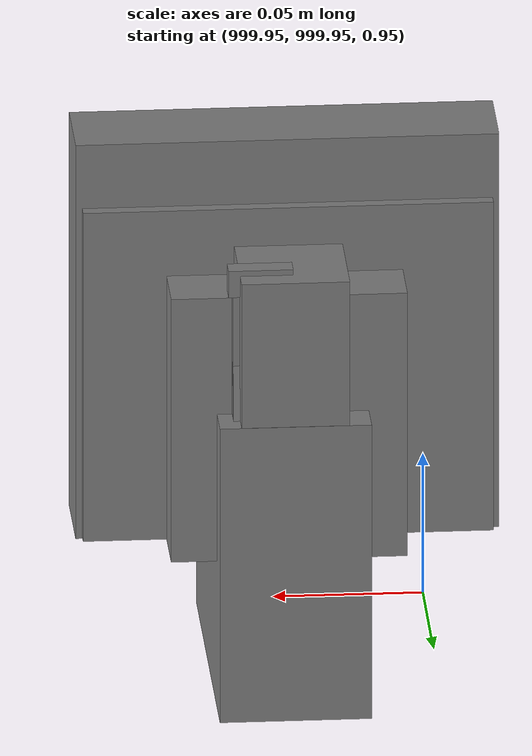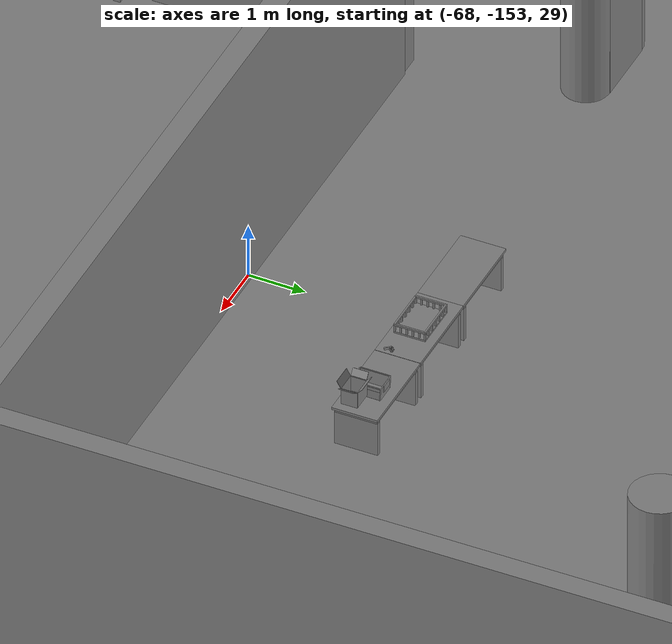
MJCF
<mujoco>
    <option gravity="0.000000000 0.000000000 -9.810000420" timestep="0.0049999999" integrator="implicitfast" density="1.225" viscosity="1.8000001e-05" noslip_iterations="10" iterations="100" sdf_iterations="50">
        <flag multiccd="disable"/>
    </option>
    <size memory="1000M"/>
    <compiler coordinate="local"/>
    <worldbody>
        <light cutoff="30" pos="0 1 1" dir="0 -1 -2"/>
        <light cutoff="30" pos="0 -1 1" dir="0 1 -2"/>
        <body pos="1000.000000000 1000.000000000 1.000000000" euler="0.000000000 0.000000000 180.000000000" name="openloong_gripper_2f85_fix_base_usda_cpu_fan">
            <geom contype="1" conaffinity="1" density="1000" type="box" material="" rgba="0.500000000 0.500000000 0.500000000 1.000000000" solimp="0.899999976 0.949999988 0.001000000" friction="1.000000000 0.005000000 0.000100000" solref="0.020000000 1.000000000" margin="0" condim="3" group="0" pos="0.000000000 0.000000000 0.070034981" quat="0.000000000 0.000000000 0.000000000 1.000000000" size="0.070700005 0.014699999 0.070700005" name="openloong_gripper_2f85_fix_base_usda_geom_1C0D7B37_A9FC_4F2C_AC16_F60C08B2C170"/>
            <freejoint name="openloong_gripper_2f85_fix_base_usda_cpu_fan_joint"/>
            <site size="0.005000000 0.005000000 0.005000000" rgba="0.500000000 0.500000000 0.500000000 1.000000000" pos="0.000000000 0.000000000 0.000000000" quat="0.999961913 0.008726535 0.000000000 0.000000000" group="0" type="sphere" name="openloong_gripper_2f85_fix_base_usda_cpu_fancsite"/>
        </body>
        <body pos="-66.000793457 -149.155014038 31.165908813" euler="-157.261322021 45.739761353 43.176948547" mocap="true" name="spotlight3_SpotLight"/>
        <body pos="1000.000000000 1000.000000000 1.000000000" euler="0.000000000 0.000000000 180.000000000" name="openloong_gripper_2f85_fix_base_usda_battery_01">
            <geom contype="1" conaffinity="1" density="1000" type="box" material="" rgba="0.500000000 0.500000000 0.500000000 1.000000000" solimp="0.899999976 0.949999988 0.001000000" friction="1.000000000 0.005000000 0.000100000" solref="0.020000000 1.000000000" margin="0" condim="3" group="0" pos="-0.011123657 -0.041940309 0.101691343" quat="1.000000000 0.000000000 0.000000000 0.000000000" size="0.010800000 0.003375000 0.004725000" name="openloong_gripper_2f85_fix_base_usda_geom_4C3171A6_59A4_4B95_9F4B_39D43625D27A"/>
            <geom contype="1" conaffinity="1" density="1000" type="box" material="" rgba="0.500000000 0.500000000 0.500000000 1.000000000" solimp="0.899999976 0.949999988 0.001000000" friction="1.000000000 0.005000000 0.000100000" solref="0.020000000 1.000000000" margin="0" condim="3" group="0" pos="-0.010876465 -0.044247437 0.047066893" quat="0.998702705 -0.050920475 0.000000000 0.000000000" size="0.009450001 0.002700000 0.024975000" name="openloong_gripper_2f85_fix_base_usda_geom_EEB95907_3D81_4F7D_B8AE_9B69E30A7830"/>
            <geom contype="1" conaffinity="1" density="1000" type="box" material="" rgba="0.500000000 0.500000000 0.500000000 1.000000000" solimp="0.899999976 0.949999988 0.001000000" friction="1.000000000 0.005000000 0.000100000" solref="0.020000000 1.000000000" margin="0" condim="3" group="0" pos="-0.001235962 -0.000659180 0.047381196" quat="1.000000000 0.000000000 0.000000000 0.000000000" size="0.039420001 0.039150000 0.047250003" name="openloong_gripper_2f85_fix_base_usda_geom_9ED4CD2B_001E_4BA0_B6A0_2C477F9E6646"/>
            <geom contype="1" conaffinity="1" density="1000" type="box" material="" rgba="0.500000000 0.500000000 0.500000000 1.000000000" solimp="0.899999976 0.949999988 0.001000000" friction="1.000000000 0.005000000 0.000100000" solref="0.020000000 1.000000000" margin="0" condim="3" group="0" pos="-0.010876465 -0.039138794 0.009851727" quat="1.000000000 0.000000000 0.000000000 0.000000000" size="0.009450001 0.010800000 0.013500000" name="openloong_gripper_2f85_fix_base_usda_geom_CD11CC14_9CEC_44BA_A490_1529DE7B7F04"/>
            <geom contype="1" conaffinity="1" density="1000" type="box" material="" rgba="0.500000000 0.500000000 0.500000000 1.000000000" solimp="0.899999976 0.949999988 0.001000000" friction="1.000000000 0.005000000 0.000100000" solref="0.020000000 1.000000000" margin="0" condim="3" group="0" pos="-0.010876465 -0.041528322 0.071508206" quat="1.000000000 0.000000000 0.000000000 0.000000000" size="0.009450001 0.002700000 0.027000001" name="openloong_gripper_2f85_fix_base_usda_geom_CF45AE28_FB6E_4657_B545_514B8A1FED5D"/>
            <freejoint name="openloong_gripper_2f85_fix_base_usda_battery_01_joint"/>
            <site size="0.005000000 0.005000000 0.005000000" rgba="0.500000000 0.500000000 0.500000000 1.000000000" pos="0.000000000 0.000000000 0.000000000" quat="0.999961913 0.008726500 0.000000000 0.000000000" group="0" type="sphere" name="openloong_gripper_2f85_fix_base_usda_battery_01site"/>
        </body>
        <body pos="1000.000000000 1000.000000000 1.000000000" euler="0.000000000 0.000000000 180.000000000" name="openloong_gripper_2f85_fix_base_usda_wifi_box">
            <geom contype="1" conaffinity="1" density="1000" type="box" material="" rgba="0.500000000 0.500000000 0.500000000 1.000000000" solimp="0.899999976 0.949999988 0.001000000" friction="1.000000000 0.005000000 0.000100000" solref="0.020000000 1.000000000" margin="0" condim="3" group="0" pos="0.000000000 0.000000000 0.058978677" quat="0.000000000 0.000000047 0.000000000 1.000000000" size="0.068499997 0.018999999 0.059000000" name="openloong_gripper_2f85_fix_base_usda_geom_82115E0D_FE95_4376_B083_7A41A37AF28F"/>
            <freejoint name="openloong_gripper_2f85_fix_base_usda_wifi_box_joint"/>
            <site size="0.005000000 0.005000000 0.005000000" rgba="0.500000000 0.500000000 0.500000000 1.000000000" pos="0.000000000 0.000000000 0.000000000" quat="0.999961913 0.008726500 0.000000000 0.000000000" group="0" type="sphere" name="openloong_gripper_2f85_fix_base_usda_wifi_boxsite"/>
        </body>
        <body pos="-66.248268127 -149.658645630 31.163217545" euler="15.330621719 66.416679382 -35.109554291" mocap="true" name="spotlight6_SpotLight"/>
        <body pos="1000.000000000 1000.000000000 1.000000000" euler="0.000011953 0.000005123 -179.999984741" name="openloong_gripper_2f85_fix_base_usda_intel_box">
            <geom contype="1" conaffinity="1" density="1000" type="box" material="" rgba="0.500000000 0.500000000 0.500000000 1.000000000" solimp="0.899999976 0.949999988 0.001000000" friction="1.000000000 0.005000000 0.000100000" solref="0.020000000 1.000000000" margin="0" condim="3" group="0" pos="0.000000000 -0.000067139 0.000082284" quat="0.707106709 0.000000225 0.000000253 0.707106650" size="0.052800003 0.025300000 0.052800003" name="openloong_gripper_2f85_fix_base_usda_geom_6DCD6985_6E35_40EF_9B61_90ED6B480E8E"/>
            <freejoint name="openloong_gripper_2f85_fix_base_usda_intel_box_joint"/>
            <site size="0.005000000 0.005000000 0.005000000" rgba="0.500000000 0.500000000 0.500000000 1.000000000" pos="0.000000000 0.000000000 0.000000000" quat="0.999961913 0.008726500 0.000000000 0.000000000" group="0" type="sphere" name="openloong_gripper_2f85_fix_base_usda_intel_boxsite"/>
        </body>
        <body pos="-66.089729309 -149.481491089 31.165548325" euler="47.739753723 -29.237134933 94.736221313" mocap="true" name="spotlight2_SpotLight"/>
        <body pos="1000.000000000 999.999938965 1.000000000" euler="0.000000000 0.000000000 180.000000000" name="openloong_gripper_2f85_fix_base_usda_intelcore_i5">
            <geom contype="1" conaffinity="1" density="1000" type="box" material="" rgba="0.500000000 0.500000000 0.500000000 1.000000000" solimp="0.899999976 0.949999988 0.001000000" friction="1.000000000 0.005000000 0.000100000" solref="0.020000000 1.000000000" margin="0" condim="3" group="0" pos="0.000000000 0.000000000 0.051722717" quat="0.707106709 0.000000000 0.000000000 -0.707106769" size="0.052800000 0.018080002 0.052800000" name="openloong_gripper_2f85_fix_base_usda_geom_8A706313_D7CC_4322_95D6_FDD8DB79FD62"/>
            <freejoint name="openloong_gripper_2f85_fix_base_usda_intelcore_i5_joint"/>
            <site size="0.005000000 0.005000000 0.005000000" rgba="0.500000000 0.500000000 0.500000000 1.000000000" pos="0.000000000 0.000000000 0.000000000" quat="0.999961913 0.008726534 0.000000000 0.000000000" group="0" type="sphere" name="openloong_gripper_2f85_fix_base_usda_intelcore_i5site"/>
        </body>
        <body pos="-64.866622925 -149.383972168 30.183746338" euler="89.999984741 89.999946594 0.000000000" name="openloong_gripper_2f85_fix_base_usda_bluebox_01">
            <geom contype="1" conaffinity="1" density="1000" type="box" material="" rgba="0.500000000 0.500000000 0.500000000 1.000000000" solimp="0.899999976 0.949999988 0.001000000" friction="1.000000000 0.005000000 0.000100000" solref="0.020000000 1.000000000" margin="0" condim="3" group="0" pos="0.276580811 0.187225342 0.000068665" quat="0.707106948 0.000077471 0.707106352 0.000077486" size="0.100000001 0.057999998 0.010000000" name="openloong_gripper_2f85_fix_base_usda_geom_FCA91B88_4B32_4FF3_863E_74F69A8321B4"/>
            <geom contype="1" conaffinity="1" density="1000" type="box" material="" rgba="0.500000000 0.500000000 0.500000000 1.000000000" solimp="0.899999976 0.949999988 0.001000000" friction="1.000000000 0.005000000 0.000100000" solref="0.020000000 1.000000000" margin="0" condim="3" group="0" pos="0.000000000 0.002883911 0.000000000" quat="0.999999881 0.000000000 0.000000000 0.000000000" size="0.254000008 0.003000000 0.172000006" name="openloong_gripper_2f85_fix_base_usda_geom_DBDAB23C_F428_4628_BD5B_D359E7D05133"/>
            <geom contype="1" conaffinity="1" density="1000" type="box" material="" rgba="0.500000000 0.500000000 0.500000000 1.000000000" solimp="0.899999976 0.949999988 0.001000000" friction="1.000000000 0.005000000 0.000100000" solref="0.020000000 1.000000000" margin="0" condim="3" group="0" pos="0.000000000 0.124874115 0.173484802" quat="0.999796331 0.020176515 -0.000000015 0.000000030" size="0.259999990 0.119999997 0.007000000" name="openloong_gripper_2f85_fix_base_usda_geom_A757D4E3_481B_42D1_95F8_94B99E23780B"/>
            <geom contype="1" conaffinity="1" density="1000" type="box" material="" rgba="0.500000000 0.500000000 0.500000000 1.000000000" solimp="0.899999976 0.949999988 0.001000000" friction="1.000000000 0.005000000 0.000100000" solref="0.020000000 1.000000000" margin="0" condim="3" group="0" pos="0.000000000 0.124874115 -0.173469543" quat="0.999796331 -0.020176545 -0.000000015 0.000000000" size="0.259999990 0.119999997 0.007000000" name="openloong_gripper_2f85_fix_base_usda_geom_A062C335_8A19_4794_B027_5F26ADD3D543"/>
            <geom contype="1" conaffinity="1" density="1000" type="box" material="" rgba="0.500000000 0.500000000 0.500000000 1.000000000" solimp="0.899999976 0.949999988 0.001000000" friction="1.000000000 0.005000000 0.000100000" solref="0.020000000 1.000000000" margin="0" condim="3" group="0" pos="0.000000000 0.214008331 0.188980103" quat="0.999912977 0.013176724 0.000000015 0.000000000" size="0.259999990 0.029999999 0.012500000" name="openloong_gripper_2f85_fix_base_usda_geom_C049E746_9F3A_4838_853F_97E669DE9D13"/>
            <geom contype="1" conaffinity="1" density="1000" type="box" material="" rgba="0.500000000 0.500000000 0.500000000 1.000000000" solimp="0.899999976 0.949999988 0.001000000" friction="1.000000000 0.005000000 0.000100000" solref="0.020000000 1.000000000" margin="0" condim="3" group="0" pos="-0.258361816 0.125289917 0.001876831" quat="0.702796936 -0.020792112 0.710783124 0.020769298" size="0.189999998 0.119999997 0.009000000" name="openloong_gripper_2f85_fix_base_usda_geom_371F6967_D87A_4661_AD50_A2FE3CFAC336"/>
            <geom contype="1" conaffinity="1" density="1000" type="box" material="" rgba="0.500000000 0.500000000 0.500000000 1.000000000" solimp="0.899999976 0.949999988 0.001000000" friction="1.000000000 0.005000000 0.000100000" solref="0.020000000 1.000000000" margin="0" condim="3" group="0" pos="0.000000000 0.214008331 -0.188980103" quat="0.999912977 -0.013176769 0.000000030 0.000000015" size="0.259999990 0.029999999 0.012500000" name="openloong_gripper_2f85_fix_base_usda_geom_088A02B0_2F69_48CD_8C9E_2FC3AA2F383E"/>
            <geom contype="1" conaffinity="1" density="1000" type="box" material="" rgba="0.500000000 0.500000000 0.500000000 1.000000000" solimp="0.899999976 0.949999988 0.001000000" friction="1.000000000 0.005000000 0.000100000" solref="0.020000000 1.000000000" margin="0" condim="3" group="0" pos="-0.276611328 0.187225342 0.000068665" quat="0.707106650 0.000077441 0.707106709 0.000077456" size="0.100000001 0.057999998 0.010000000" name="openloong_gripper_2f85_fix_base_usda_geom_6584A0E4_B5DB_416C_ACCB_93EE6AC0ACBF"/>
            <geom contype="1" conaffinity="1" density="1000" type="box" material="" rgba="0.500000000 0.500000000 0.500000000 1.000000000" solimp="0.899999976 0.949999988 0.001000000" friction="1.000000000 0.005000000 0.000100000" solref="0.020000000 1.000000000" margin="0" condim="3" group="0" pos="0.258331299 0.125289917 0.001876831" quat="0.702851415 0.018856421 0.710823774 -0.019329369" size="0.189999998 0.119999997 0.009000000" name="openloong_gripper_2f85_fix_base_usda_geom_9BB35E73_3D43_4E21_BF72_6DCE0358633C"/>
            <freejoint name="openloong_gripper_2f85_fix_base_usda_bluebox_01_joint"/>
            <site size="0.005000000 0.005000000 0.005000000" rgba="0.500000000 0.500000000 0.500000000 1.000000000" pos="0.000000000 0.000000000 0.000000000" quat="0.999961913 0.008726534 0.000000000 0.000000000" group="0" type="sphere" name="openloong_gripper_2f85_fix_base_usda_bluebox_01site"/>
        </body>
        <body pos="-64.496299744 -149.491867065 30.235729218" euler="0.000000000 0.000000000 89.999946594" name="openloong_gripper_2f85_fix_base_usda_cardboardbox_01">
            <geom contype="1" conaffinity="1" density="1000" type="box" material="" rgba="0.500000000 0.500000000 0.500000000 1.000000000" solimp="0.899999976 0.949999988 0.001000000" friction="1.000000000 0.005000000 0.000100000" solref="0.020000000 1.000000000" margin="0" condim="3" group="0" pos="-0.003166199 -0.004086494 0.005052090" quat="1.000000000 0.000000000 0.000000000 0.000000000" size="0.142499998 0.177500010 0.005000000" name="openloong_gripper_2f85_fix_base_usda_geom_83E39F3A_E636_4B82_81FA_787B612258F6"/>
            <geom contype="1" conaffinity="1" density="1000" type="box" material="" rgba="0.500000000 0.500000000 0.500000000 1.000000000" solimp="0.899999976 0.949999988 0.001000000" friction="1.000000000 0.005000000 0.000100000" solref="0.020000000 1.000000000" margin="0" condim="3" group="0" pos="-0.003166199 0.170316696 0.150570869" quat="1.000000000 0.000000000 0.000000000 0.000000000" size="0.142499998 0.005000000 0.149999991" name="openloong_gripper_2f85_fix_base_usda_geom_3191D84B_53F9_45B8_B4C0_08097066A27F"/>
            <geom contype="1" conaffinity="1" density="1000" type="box" material="" rgba="0.500000000 0.500000000 0.500000000 1.000000000" solimp="0.899999976 0.949999988 0.001000000" friction="1.000000000 0.005000000 0.000100000" solref="0.020000000 1.000000000" margin="0" condim="3" group="0" pos="-0.147399902 -0.005307198 0.150570869" quat="1.000000000 0.000000000 0.000000000 0.000000000" size="0.005000000 0.177500010 0.149999991" name="openloong_gripper_2f85_fix_base_usda_geom_CAC3BFF6_4C36_4070_A5BE_82544E5FE7F9"/>
            <geom contype="1" conaffinity="1" density="1000" type="box" material="" rgba="0.500000000 0.500000000 0.500000000 1.000000000" solimp="0.899999976 0.949999988 0.001000000" friction="1.000000000 0.005000000 0.000100000" solref="0.020000000 1.000000000" margin="0" condim="3" group="0" pos="0.140275955 -0.005307198 0.150570869" quat="1.000000000 0.000000000 0.000000000 0.000000000" size="0.005000000 0.177500010 0.149999991" name="openloong_gripper_2f85_fix_base_usda_geom_6960868C_A7A6_44D8_ADE2_2471B92D3619"/>
            <geom contype="1" conaffinity="1" density="1000" type="box" material="" rgba="0.500000000 0.500000000 0.500000000 1.000000000" solimp="0.899999976 0.949999988 0.001000000" friction="1.000000000 0.005000000 0.000100000" solref="0.020000000 1.000000000" margin="0" condim="3" group="0" pos="-0.003166199 -0.181550980 0.150570869" quat="1.000000000 0.000000000 0.000000000 0.000000000" size="0.142499998 0.005000000 0.149999991" name="openloong_gripper_2f85_fix_base_usda_geom_CB6CF59A_9E49_48DC_B617_97E01BCCFF75"/>
            <freejoint name="openloong_gripper_2f85_fix_base_usda_cardboardbox_01_joint"/>
            <site size="0.005000000 0.005000000 0.005000000" rgba="0.500000000 0.500000000 0.500000000 1.000000000" pos="0.000000000 0.000000000 0.000000000" quat="0.999961913 0.008726535 0.000000000 0.000000000" group="0" type="sphere" name="openloong_gripper_2f85_fix_base_usda_site_72D29554_003A_453E_8F6F_0D2032F043B0"/>
            <body pos="0.139160156 -0.004048347 0.301930904" euler="-179.999954224 49.383502960 179.999954224" name="openloong_gripper_2f85_fix_base_usda_A1_006">
                <geom contype="1" conaffinity="1" density="1000" type="box" material="" rgba="0.500000000 0.500000000 0.500000000 1.000000000" solimp="0.899999976 0.949999988 0.001000000" friction="1.000000000 0.005000000 0.000100000" solref="0.020000000 1.000000000" margin="0" condim="3" group="0" pos="-0.071587563 0.000009537 0.001745224" quat="0.999999881 0.000000000 0.000000000 0.000000000" size="0.071249999 0.179999992 0.002500000" name="openloong_gripper_2f85_fix_base_usda_geom_E3202FBA_35C5_40F8_B5C1_2C0D36871C1B"/>
                <joint armature="0" stiffness="0.07" damping="0.0099999998" axis="0.000000 1.000000 0.000000" type="hinge" name="openloong_gripper_2f85_fix_base_usda_A1_006"/>
            </body>
            <body pos="-0.145902634 -0.004086494 0.301938057" euler="-180.000000000 -60.000011444 -180.000000000" name="openloong_gripper_2f85_fix_base_usda_A2_006">
                <geom contype="1" conaffinity="1" density="1000" type="box" material="" rgba="0.500000000 0.500000000 0.500000000 1.000000000" solimp="0.899999976 0.949999988 0.001000000" friction="1.000000000 0.005000000 0.000100000" solref="0.020000000 1.000000000" margin="0" condim="3" group="0" pos="0.071268082 0.000009537 0.002717972" quat="0.000002921 0.000000000 -0.000000030 0.999999881" size="0.071249999 0.179999992 0.002500000" name="openloong_gripper_2f85_fix_base_usda_geom_7A7E52E2_398E_43CD_ABAA_7F4772466E6C"/>
                <joint armature="0" stiffness="0.07" damping="0.0099999998" axis="0.000000 1.000000 0.000000" type="hinge" name="openloong_gripper_2f85_fix_base_usda_A2_006"/>
            </body>
            <body pos="-0.003385544 0.175991058 0.301930904" euler="-125.858116150 -0.000004561 0.000002331" name="openloong_gripper_2f85_fix_base_usda_B2_006">
                <geom contype="1" conaffinity="1" density="1000" type="box" material="" rgba="0.500000000 0.500000000 0.500000000 1.000000000" solimp="0.899999976 0.949999988 0.001000000" friction="1.000000000 0.005000000 0.000100000" solref="0.020000000 1.000000000" margin="0" condim="3" group="0" pos="0.000009537 -0.070939064 -0.002470016" quat="0.999614120 0.027776197 -0.000000015 0.000000030" size="0.137500003 0.064999998 0.005000000" name="openloong_gripper_2f85_fix_base_usda_geom_41D89EC6_BDEF_4D78_9031_F493D5174476"/>
                <joint armature="0" stiffness="0.07" damping="0.0099999998" axis="1.000000 0.000000 0.000000" type="hinge" name="openloong_gripper_2f85_fix_base_usda_B2_006"/>
            </body>
            <body pos="-0.003385544 -0.184140205 0.301938057" euler="147.805557251 0.000000000 0.000000000" name="openloong_gripper_2f85_fix_base_usda_B1_006">
                <geom contype="1" conaffinity="1" density="1000" type="box" material="" rgba="0.500000000 0.500000000 0.500000000 1.000000000" solimp="0.899999976 0.949999988 0.001000000" friction="1.000000000 0.005000000 0.000100000" solref="0.020000000 1.000000000" margin="0" condim="3" group="0" pos="-0.000028610 0.070202351 -0.002703667" quat="0.999614179 -0.027776167 0.000000000 0.000000000" size="0.137500003 0.064999998 0.005000000" name="openloong_gripper_2f85_fix_base_usda_geom_349617BA_2D89_4EB1_A148_E2E23C52DC5D"/>
                <joint armature="0" stiffness="0.07" damping="0.0099999998" axis="1.000000 0.000000 0.000000" type="hinge" name="openloong_gripper_2f85_fix_base_usda_B1_006"/>
            </body>
        </body>
        <body pos="-65.882858276 -149.481979370 30.229999542" euler="-64.487716675 0.000000000 0.000000000" name="openloong_gripper_2f85_fix_base_usda_Barcode">
            <geom contype="1" conaffinity="1" density="1000" type="box" material="" rgba="0.500000000 0.500000000 0.500000000 1.000000000" solimp="0.899999976 0.949999988 0.001000000" friction="1.000000000 0.005000000 0.000100000" solref="0.020000000 1.000000000" margin="0" condim="3" group="0" pos="0.000000000 0.013038635 0.001419067" quat="0.000000000 0.000000000 0.000000000 1.000000119" size="0.034000002 0.010000000 0.017999999" name="openloong_gripper_2f85_fix_base_usda_geom_BBC35A5A_AE78_4A18_B631_E1320B697764"/>
            <geom contype="1" conaffinity="1" density="1000" type="box" material="" rgba="0.500000000 0.500000000 0.500000000 1.000000000" solimp="0.899999976 0.949999988 0.001000000" friction="1.000000000 0.005000000 0.000100000" solref="0.020000000 1.000000000" margin="0" condim="3" group="0" pos="0.000000000 -0.035301208 -0.007095337" quat="0.000000000 0.000000000 -0.043619365 0.999048233" size="0.028999999 0.010000000 0.020000000" name="openloong_gripper_2f85_fix_base_usda_geom_AD29BDA5_8374_4479_95A7_EACC4508E93F"/>
            <geom contype="1" conaffinity="1" density="1000" type="box" material="" rgba="0.500000000 0.500000000 0.500000000 1.000000000" solimp="0.899999976 0.949999988 0.001000000" friction="1.000000000 0.005000000 0.000100000" solref="0.020000000 1.000000000" margin="0" condim="3" group="0" pos="0.000000000 -0.043411255 -0.011749268" quat="0.922262907 0.386563420 0.000000000 0.000000000" size="0.026000001 0.010000000 0.020000000" name="openloong_gripper_2f85_fix_base_usda_geom_E77E3080_6EA1_457C_A077_767EB4EBA83E"/>
            <geom contype="1" conaffinity="1" density="1000" type="box" material="" rgba="0.500000000 0.500000000 0.500000000 1.000000000" solimp="0.899999976 0.949999988 0.001000000" friction="1.000000000 0.005000000 0.000100000" solref="0.020000000 1.000000000" margin="0" condim="3" group="0" pos="0.000000000 -0.016967773 -0.031860352" quat="0.000000000 0.000000000 0.000000000 1.000000119" size="0.008000000 0.010000000 0.013000000" name="openloong_gripper_2f85_fix_base_usda_geom_465B381D_F5D1_4BCD_8AB0_8A727448CA9B"/>
            <geom contype="1" conaffinity="1" density="1000" type="box" material="" rgba="0.500000000 0.500000000 0.500000000 1.000000000" solimp="0.899999976 0.949999988 0.001000000" friction="1.000000000 0.005000000 0.000100000" solref="0.020000000 1.000000000" margin="0" condim="3" group="0" pos="0.000000000 -0.001869202 0.000312805" quat="0.953716993 0.300705761 0.000000000 0.000000000" size="0.032000002 0.010000000 0.018999999" name="openloong_gripper_2f85_fix_base_usda_geom_6C833342_2BDD_4DC0_830B_697022CED19A"/>
            <geom contype="1" conaffinity="1" density="1000" type="box" material="" rgba="0.500000000 0.500000000 0.500000000 1.000000000" solimp="0.899999976 0.949999988 0.001000000" friction="1.000000000 0.005000000 0.000100000" solref="0.020000000 1.000000000" margin="0" condim="3" group="0" pos="0.000000000 -0.019531250 -0.003173828" quat="0.953716993 0.300705761 0.000000000 0.000000000" size="0.030999999 0.010000000 0.020000000" name="openloong_gripper_2f85_fix_base_usda_geom_5A53E3E3_0D52_45D5_8A31_6AE2D87C7D6C"/>
            <geom contype="1" conaffinity="1" density="1000" type="box" material="" rgba="0.500000000 0.500000000 0.500000000 1.000000000" solimp="0.899999976 0.949999988 0.001000000" friction="1.000000000 0.005000000 0.000100000" solref="0.020000000 1.000000000" margin="0" condim="3" group="0" pos="0.000000000 -0.035301208 -0.007095337" quat="0.953716993 0.300705761 0.000000000 0.000000000" size="0.028999999 0.010000000 0.020000000" name="openloong_gripper_2f85_fix_base_usda_geom_5E0998AE_763E_42AE_B983_8BDD2CD9C606"/>
            <geom contype="1" conaffinity="1" density="1000" type="box" material="" rgba="0.500000000 0.500000000 0.500000000 1.000000000" solimp="0.899999976 0.949999988 0.001000000" friction="1.000000000 0.005000000 0.000100000" solref="0.020000000 1.000000000" margin="0" condim="3" group="0" pos="0.000000000 -0.042617798 -0.071121216" quat="0.000000000 0.000000000 0.000000000 1.000000119" size="0.013000000 0.021000000 0.059999999" name="openloong_gripper_2f85_fix_base_usda_geom_E00D2B45_6753_4AE0_B134_29BC3BAC88A6"/>
            <freejoint name="openloong_gripper_2f85_fix_base_usda_Barcode_joint"/>
            <site size="0.005000000 0.005000000 0.005000000" rgba="0.500000000 0.500000000 0.500000000 1.000000000" pos="0.000000000 0.000000000 0.000000000" quat="1.000000000 0.000000000 0.000000000 0.000000000" group="0" type="sphere" name="openloong_gripper_2f85_fix_base_usda_Barcode_site"/>
        </body>
        <body pos="-66.745018005 -149.392349243 30.184000015" euler="0.000000000 0.000000000 89.999946594" name="[22329922602583]_Basket_01">
            <geom contype="1" conaffinity="1" density="1000" type="box" material="" rgba="0.500000000 0.500000000 0.500000000 1.000000000" solimp="0.899999976 0.949999988 0.001000000" friction="1.000000000 0.005000000 0.000100000" solref="0.020000000 1.000000000" margin="0" condim="3" group="0" pos="-0.052425385 0.389207840 0.089787483" quat="0.707107008 0.000000000 0.000000000 0.707106411" size="0.014249999 0.014249999 0.059999999" name="[22329922602583]_geom_CA9C3EA3_1B07_41AB_9273_5E9055D5F465"/>
            <geom contype="1" conaffinity="1" density="1000" type="box" material="" rgba="0.500000000 0.500000000 0.500000000 1.000000000" solimp="0.899999976 0.949999988 0.001000000" friction="1.000000000 0.005000000 0.000100000" solref="0.020000000 1.000000000" margin="0" condim="3" group="0" pos="0.264015198 -0.133043289 0.089787483" quat="0.707107008 0.000000000 0.000000000 0.707106411" size="0.014249999 0.014249999 0.059999999" name="[22329922602583]_geom_BABBD4CF_4E61_4327_AA08_233B272BD42C"/>
            <geom contype="1" conaffinity="1" density="1000" type="box" material="" rgba="0.500000000 0.500000000 0.500000000 1.000000000" solimp="0.899999976 0.949999988 0.001000000" friction="1.000000000 0.005000000 0.000100000" solref="0.020000000 1.000000000" margin="0" condim="3" group="0" pos="-0.264015198 -0.265548706 0.089793205" quat="0.707107008 0.000000000 0.000000000 0.707106411" size="0.014249999 0.014249999 0.059999999" name="[22329922602583]_geom_5272CEAF_0C91_462D_BBF5_D550B058A5D5"/>
            <geom contype="1" conaffinity="1" density="1000" type="box" material="" rgba="0.500000000 0.500000000 0.500000000 1.000000000" solimp="0.899999976 0.949999988 0.001000000" friction="1.000000000 0.005000000 0.000100000" solref="0.020000000 1.000000000" margin="0" condim="3" group="0" pos="-0.160263062 -0.389322281 0.089793205" quat="0.707107008 0.000000000 0.000000000 0.707106411" size="0.014249999 0.014249999 0.059999999" name="[22329922602583]_geom_55C183A2_A644_4DB8_B44A_4370E7435DC4"/>
            <geom contype="1" conaffinity="1" density="1000" type="box" material="" rgba="0.500000000 0.500000000 0.500000000 1.000000000" solimp="0.899999976 0.949999988 0.001000000" friction="1.000000000 0.005000000 0.000100000" solref="0.020000000 1.000000000" margin="0" condim="3" group="0" pos="0.162265778 -0.389322281 0.089787483" quat="0.707107008 0.000000000 0.000000000 0.707106411" size="0.014249999 0.014249999 0.059999999" name="[22329922602583]_geom_F817D334_2283_4A56_A85A_514D626FEBD3"/>
            <geom contype="1" conaffinity="1" density="1000" type="box" material="" rgba="0.500000000 0.500000000 0.500000000 1.000000000" solimp="0.899999976 0.949999988 0.001000000" friction="1.000000000 0.005000000 0.000100000" solref="0.020000000 1.000000000" margin="0" condim="3" group="0" pos="0.264015198 0.389207840 0.089787483" quat="0.707107008 0.000000000 0.000000000 0.707106411" size="0.014249999 0.014249999 0.059999999" name="[22329922602583]_geom_F9F1A9D2_DCA3_4DEF_B303_C250035B65BD"/>
            <geom contype="1" conaffinity="1" density="1000" type="box" material="" rgba="0.500000000 0.500000000 0.500000000 1.000000000" solimp="0.899999976 0.949999988 0.001000000" friction="1.000000000 0.005000000 0.000100000" solref="0.020000000 1.000000000" margin="0" condim="3" group="0" pos="-0.264015198 -0.133043289 0.089793205" quat="0.707107008 0.000000000 0.000000000 0.707106411" size="0.014249999 0.014249999 0.059999999" name="[22329922602583]_geom_A8E0D4DE_FC7B_4B38_A9E7_CA1C150D6DF7"/>
            <geom contype="1" conaffinity="1" density="1000" type="box" material="" rgba="0.500000000 0.500000000 0.500000000 1.000000000" solimp="0.899999976 0.949999988 0.001000000" friction="1.000000000 0.005000000 0.000100000" solref="0.020000000 1.000000000" margin="0" condim="3" group="0" pos="-0.264026642 0.269256592 0.089793205" quat="0.707107008 0.000000000 0.000000000 0.707106411" size="0.014249999 0.014249999 0.059999999" name="[22329922602583]_geom_CCD6A7E5_5E7A_4ED3_9B2D_4A3C639D655A"/>
            <geom contype="1" conaffinity="1" density="1000" type="box" material="" rgba="0.500000000 0.500000000 0.500000000 1.000000000" solimp="0.899999976 0.949999988 0.001000000" friction="1.000000000 0.005000000 0.000100000" solref="0.020000000 1.000000000" margin="0" condim="3" group="0" pos="0.054462433 0.389207840 0.089787483" quat="0.707107008 0.000000000 0.000000000 0.707106411" size="0.014249999 0.014249999 0.059999999" name="[22329922602583]_geom_23DD9D39_6329_4E4D_AC93_9D817A41396B"/>
            <geom contype="1" conaffinity="1" density="1000" type="box" material="" rgba="0.500000000 0.500000000 0.500000000 1.000000000" solimp="0.899999976 0.949999988 0.001000000" friction="1.000000000 0.005000000 0.000100000" solref="0.020000000 1.000000000" margin="0" condim="3" group="0" pos="0.054462433 -0.389322281 0.089787483" quat="0.707107008 0.000000000 0.000000000 0.707106411" size="0.014249999 0.014249999 0.059999999" name="[22329922602583]_geom_56E0E4B1_F8F0_4D0D_8FA4_6FA272D86BB1"/>
            <geom contype="1" conaffinity="1" density="1000" type="box" material="" rgba="0.500000000 0.500000000 0.500000000 1.000000000" solimp="0.899999976 0.949999988 0.001000000" friction="1.000000000 0.005000000 0.000100000" solref="0.020000000 1.000000000" margin="0" condim="3" group="0" pos="0.264015198 0.269256592 0.089793205" quat="0.707107008 0.000000000 0.000000000 0.707106411" size="0.014249999 0.014249999 0.059999999" name="[22329922602583]_geom_6D777B51_E74E_40D7_ADE1_2813CBC20174"/>
            <geom contype="1" conaffinity="1" density="1000" type="box" material="" rgba="0.500000000 0.500000000 0.500000000 1.000000000" solimp="0.899999976 0.949999988 0.001000000" friction="1.000000000 0.005000000 0.000100000" solref="0.020000000 1.000000000" margin="0" condim="3" group="0" pos="0.264015198 -0.389322281 0.089787483" quat="0.707107008 0.000000000 0.000000000 0.707106411" size="0.014249999 0.014249999 0.059999999" name="[22329922602583]_geom_2BF93125_EC4B_4710_9369_4138F104129A"/>
            <geom contype="1" conaffinity="1" density="1000" type="box" material="" rgba="0.500000000 0.500000000 0.500000000 1.000000000" solimp="0.899999976 0.949999988 0.001000000" friction="1.000000000 0.005000000 0.000100000" solref="0.020000000 1.000000000" margin="0" condim="3" group="0" pos="0.000000000 0.000000000 0.015998840" quat="0.707107008 0.000000000 0.000000000 0.707106411" size="0.403499991 0.279000014 0.015750000" name="[22329922602583]_geom_E6FEE2F9_DC9A_46B2_BBB5_8D393A68E59C"/>
            <geom contype="1" conaffinity="1" density="1000" type="box" material="" rgba="0.500000000 0.500000000 0.500000000 1.000000000" solimp="0.899999976 0.949999988 0.001000000" friction="1.000000000 0.005000000 0.000100000" solref="0.020000000 1.000000000" margin="0" condim="3" group="0" pos="0.000000000 -0.389476776 0.163619041" quat="0.707107008 0.000000000 0.000000000 0.707106411" size="0.015000000 0.277500004 0.015750000" name="[22329922602583]_geom_0CD70745_EBCE_4B2E_AAC3_C4F620670DB4"/>
            <geom contype="1" conaffinity="1" density="1000" type="box" material="" rgba="0.500000000 0.500000000 0.500000000 1.000000000" solimp="0.899999976 0.949999988 0.001000000" friction="1.000000000 0.005000000 0.000100000" solref="0.020000000 1.000000000" margin="0" condim="3" group="0" pos="0.162265778 0.389207840 0.089787483" quat="0.707107008 0.000000000 0.000000000 0.707106411" size="0.014249999 0.014249999 0.059999999" name="[22329922602583]_geom_F5264DAF_F88B_453A_A123_276B72E2A90A"/>
            <geom contype="1" conaffinity="1" density="1000" type="box" material="" rgba="0.500000000 0.500000000 0.500000000 1.000000000" solimp="0.899999976 0.949999988 0.001000000" friction="1.000000000 0.005000000 0.000100000" solref="0.020000000 1.000000000" margin="0" condim="3" group="0" pos="0.000000000 0.389471054 0.163619041" quat="0.707107008 0.000000000 0.000000000 0.707106411" size="0.015000000 0.277500004 0.015750000" name="[22329922602583]_geom_94372A06_262E_4BFA_83C4_F7B361C60E95"/>
            <geom contype="1" conaffinity="1" density="1000" type="box" material="" rgba="0.500000000 0.500000000 0.500000000 1.000000000" solimp="0.899999976 0.949999988 0.001000000" friction="1.000000000 0.005000000 0.000100000" solref="0.020000000 1.000000000" margin="0" condim="3" group="0" pos="-0.263511658 0.000000000 0.163619041" quat="0.707107008 0.000000000 0.000000000 0.707106411" size="0.403499991 0.015000000 0.015750000" name="[22329922602583]_geom_C5BA600A_9AB7_4B5A_86F8_BFD429B3D937"/>
            <geom contype="1" conaffinity="1" density="1000" type="box" material="" rgba="0.500000000 0.500000000 0.500000000 1.000000000" solimp="0.899999976 0.949999988 0.001000000" friction="1.000000000 0.005000000 0.000100000" solref="0.020000000 1.000000000" margin="0" condim="3" group="0" pos="-0.264015198 0.141334534 0.089793205" quat="0.707107008 0.000000000 0.000000000 0.707106411" size="0.014249999 0.014249999 0.059999999" name="[22329922602583]_geom_F21733AF_EA5E_4738_8692_9BA9C6CB8920"/>
            <geom contype="1" conaffinity="1" density="1000" type="box" material="" rgba="0.500000000 0.500000000 0.500000000 1.000000000" solimp="0.899999976 0.949999988 0.001000000" friction="1.000000000 0.005000000 0.000100000" solref="0.020000000 1.000000000" margin="0" condim="3" group="0" pos="0.264015198 -0.265548706 0.089787483" quat="0.707107008 0.000000000 0.000000000 0.707106411" size="0.014249999 0.014249999 0.059999999" name="[22329922602583]_geom_6656E735_C114_43C9_9944_AD6F80B4A455"/>
            <geom contype="1" conaffinity="1" density="1000" type="box" material="" rgba="0.500000000 0.500000000 0.500000000 1.000000000" solimp="0.899999976 0.949999988 0.001000000" friction="1.000000000 0.005000000 0.000100000" solref="0.020000000 1.000000000" margin="0" condim="3" group="0" pos="-0.160263062 0.389207840 0.089787483" quat="0.707107008 0.000000000 0.000000000 0.707106411" size="0.014249999 0.014249999 0.059999999" name="[22329922602583]_geom_70B11E54_3DC1_458D_B23C_F687878BDC52"/>
            <geom contype="1" conaffinity="1" density="1000" type="box" material="" rgba="0.500000000 0.500000000 0.500000000 1.000000000" solimp="0.899999976 0.949999988 0.001000000" friction="1.000000000 0.005000000 0.000100000" solref="0.020000000 1.000000000" margin="0" condim="3" group="0" pos="-0.052425385 -0.389322281 0.089787483" quat="0.707107008 0.000000000 0.000000000 0.707106411" size="0.014249999 0.014249999 0.059999999" name="[22329922602583]_geom_81BB38F3_1FDF_4965_B9F5_FF213D83F3CD"/>
            <geom contype="1" conaffinity="1" density="1000" type="box" material="" rgba="0.500000000 0.500000000 0.500000000 1.000000000" solimp="0.899999976 0.949999988 0.001000000" friction="1.000000000 0.005000000 0.000100000" solref="0.020000000 1.000000000" margin="0" condim="3" group="0" pos="-0.264026642 -0.389322281 0.089793205" quat="0.707107008 0.000000000 0.000000000 0.707106411" size="0.014249999 0.014249999 0.059999999" name="[22329922602583]_geom_711DEE06_CBA7_4BE6_935D_A8CFEE243E43"/>
            <geom contype="1" conaffinity="1" density="1000" type="box" material="" rgba="0.500000000 0.500000000 0.500000000 1.000000000" solimp="0.899999976 0.949999988 0.001000000" friction="1.000000000 0.005000000 0.000100000" solref="0.020000000 1.000000000" margin="0" condim="3" group="0" pos="0.264015198 0.141334534 0.089787483" quat="0.707107008 0.000000000 0.000000000 0.707106411" size="0.014249999 0.014249999 0.059999999" name="[22329922602583]_geom_0DF4DE16_B509_4F3E_B5F5_195FCCFE2A32"/>
            <geom contype="1" conaffinity="1" density="1000" type="box" material="" rgba="0.500000000 0.500000000 0.500000000 1.000000000" solimp="0.899999976 0.949999988 0.001000000" friction="1.000000000 0.005000000 0.000100000" solref="0.020000000 1.000000000" margin="0" condim="3" group="0" pos="-0.264015198 0.389207840 0.089793205" quat="0.707107008 0.000000000 0.000000000 0.707106411" size="0.014249999 0.014249999 0.059999999" name="[22329922602583]_geom_633A713A_75E7_4BDB_A87A_8E96E95A9C9F"/>
            <geom contype="1" conaffinity="1" density="1000" type="box" material="" rgba="0.500000000 0.500000000 0.500000000 1.000000000" solimp="0.899999976 0.949999988 0.001000000" friction="1.000000000 0.005000000 0.000100000" solref="0.020000000 1.000000000" margin="0" condim="3" group="0" pos="0.264015198 0.004480362 0.089787483" quat="0.707107008 0.000000000 0.000000000 0.707106411" size="0.014249999 0.014249999 0.059999999" name="[22329922602583]_geom_E66129C2_D245_40FE_B960_D35592F10141"/>
            <geom contype="1" conaffinity="1" density="1000" type="box" material="" rgba="0.500000000 0.500000000 0.500000000 1.000000000" solimp="0.899999976 0.949999988 0.001000000" friction="1.000000000 0.005000000 0.000100000" solref="0.020000000 1.000000000" margin="0" condim="3" group="0" pos="0.263694763 -0.000011444 0.163619041" quat="0.707107008 0.000000000 0.000000000 0.707106411" size="0.403499991 0.015000000 0.015750000" name="[22329922602583]_geom_3E6DBA14_68A4_4384_B694_CCF73BEC2380"/>
            <geom contype="1" conaffinity="1" density="1000" type="box" material="" rgba="0.500000000 0.500000000 0.500000000 1.000000000" solimp="0.899999976 0.949999988 0.001000000" friction="1.000000000 0.005000000 0.000100000" solref="0.020000000 1.000000000" margin="0" condim="3" group="0" pos="-0.264015198 0.004480362 0.089793205" quat="0.707107008 0.000000000 0.000000000 0.707106411" size="0.014249999 0.014249999 0.059999999" name="[22329922602583]_geom_34A60297_5089_46DD_9788_64900108E650"/>
            <freejoint name="[22329922602583]_joint_4BBC7988_A474_4B05_847C_CB0DEDC2CBC6"/>
        </body>
        <body pos="0.000000000 0.000000000 0.000000000" euler="0.000000000 0.000000000 0.000000000" name="Static Objects_Static Objects">
            <geom contype="1" conaffinity="1" density="1000" type="box" material="" rgba="0.500000000 0.500000000 0.500000000 1.000000000" solimp="0.899999976 0.949999988 0.001000000" friction="1.000000000 0.005000000 0.000100000" solref="0.020000000 1.000000000" margin="0" condim="3" group="0" pos="-67.544113159 -149.365814209 29.727830887" quat="0.500000417 0.499999970 0.499999553 0.499999970" size="0.381000012 0.319999993 0.041000001" name="Static Objects_geom_B7364FE1_5D9E_4BB2_BB57_AA423E09C5DD"/>
            <geom contype="1" conaffinity="1" density="1000" type="box" material="" rgba="0.500000000 0.500000000 0.500000000 1.000000000" solimp="0.899999976 0.949999988 0.001000000" friction="1.000000000 0.005000000 0.000100000" solref="0.020000000 1.000000000" margin="0" condim="3" group="0" pos="-68.239501953 -149.365814209 30.086868286" quat="0.500000417 0.499999970 0.499999553 0.499999970" size="0.370999992 0.039500002 0.745000005" name="Static Objects_geom_69CCDF4A_578B_4503_8EE0_E7039B279711"/>
            <geom contype="1" conaffinity="1" density="1000" type="box" material="" rgba="0.500000000 0.500000000 0.500000000 1.000000000" solimp="0.899999976 0.949999988 0.001000000" friction="1.000000000 0.005000000 0.000100000" solref="0.020000000 1.000000000" margin="0" condim="3" group="0" pos="-68.239501953 -149.365814209 30.147235870" quat="0.500000417 0.499999970 0.499999553 0.499999970" size="0.400000006 0.022000000 0.800000012" name="Static Objects_geom_C10CD5AE_6D28_4392_8D6A_647790AEE86D"/>
            <geom contype="1" conaffinity="1" density="1000" type="box" material="" rgba="0.500000000 0.500000000 0.500000000 1.000000000" solimp="0.899999976 0.949999988 0.001000000" friction="1.000000000 0.005000000 0.000100000" solref="0.020000000 1.000000000" margin="0" condim="3" group="0" pos="-68.934890747 -149.365814209 29.727830887" quat="0.500000417 0.499999970 0.499999553 0.499999970" size="0.381000012 0.319999993 0.041000001" name="Static Objects_geom_6F3B528F_FE08_4556_A674_8953B625CB9E"/>
            <geom contype="1" conaffinity="1" density="1000" type="box" material="" rgba="0.500000000 0.500000000 0.500000000 1.000000000" solimp="0.899999976 0.949999988 0.001000000" friction="1.000000000 0.005000000 0.000100000" solref="0.020000000 1.000000000" margin="0" condim="3" group="0" pos="-68.239501953 -149.365814209 29.561563492" quat="0.500000417 0.499999970 0.499999553 0.499999970" size="0.020000000 0.022000000 0.660000026" name="Static Objects_geom_C56B1D73_78C7_42E6_A775_A56FD993D388"/>
            <geom contype="1" conaffinity="1" density="1000" type="box" material="" rgba="0.500000000 0.500000000 0.500000000 1.000000000" solimp="0.899999976 0.949999988 0.001000000" friction="1.000000000 0.005000000 0.000100000" solref="0.020000000 1.000000000" margin="0" condim="3" group="0" pos="-65.945671082 -149.365814209 29.727830887" quat="0.500000417 0.499999970 0.499999553 0.499999970" size="0.381000012 0.319999993 0.041000001" name="Static Objects_geom_E0B543B7_6208_4764_BEA1_0C7A26AEE0B5"/>
            <geom contype="1" conaffinity="1" density="1000" type="box" material="" rgba="0.500000000 0.500000000 0.500000000 1.000000000" solimp="0.899999976 0.949999988 0.001000000" friction="1.000000000 0.005000000 0.000100000" solref="0.020000000 1.000000000" margin="0" condim="3" group="0" pos="-66.641059875 -149.365814209 30.086868286" quat="0.500000417 0.499999970 0.499999553 0.499999970" size="0.370999992 0.039500002 0.745000005" name="Static Objects_geom_5969EB08_E89A_4974_8C40_F198B109BB50"/>
            <geom contype="1" conaffinity="1" density="1000" type="box" material="" rgba="0.500000000 0.500000000 0.500000000 1.000000000" solimp="0.899999976 0.949999988 0.001000000" friction="1.000000000 0.005000000 0.000100000" solref="0.020000000 1.000000000" margin="0" condim="3" group="0" pos="-66.641059875 -149.365814209 30.147235870" quat="0.500000417 0.499999970 0.499999553 0.499999970" size="0.400000006 0.022000000 0.800000012" name="Static Objects_geom_6B545D02_8EE9_4B20_BCBC_4D506C448D6F"/>
            <geom contype="1" conaffinity="1" density="1000" type="box" material="" rgba="0.500000000 0.500000000 0.500000000 1.000000000" solimp="0.899999976 0.949999988 0.001000000" friction="1.000000000 0.005000000 0.000100000" solref="0.020000000 1.000000000" margin="0" condim="3" group="0" pos="-67.336448669 -149.365814209 29.727830887" quat="0.500000417 0.499999970 0.499999553 0.499999970" size="0.381000012 0.319999993 0.041000001" name="Static Objects_geom_78B6ACE6_D8DE_4DAB_8795_B8D67471207B"/>
            <geom contype="1" conaffinity="1" density="1000" type="box" material="" rgba="0.500000000 0.500000000 0.500000000 1.000000000" solimp="0.899999976 0.949999988 0.001000000" friction="1.000000000 0.005000000 0.000100000" solref="0.020000000 1.000000000" margin="0" condim="3" group="0" pos="-66.641059875 -149.365814209 29.561563492" quat="0.500000417 0.499999970 0.499999553 0.499999970" size="0.020000000 0.022000000 0.660000026" name="Static Objects_geom_7D53B2A4_8AF4_43B4_ABB0_350AAD34B5DF"/>
            <geom contype="1" conaffinity="1" density="1000" type="box" material="" rgba="0.500000000 0.500000000 0.500000000 1.000000000" solimp="0.899999976 0.949999988 0.001000000" friction="1.000000000 0.005000000 0.000100000" solref="0.020000000 1.000000000" margin="0" condim="3" group="0" pos="-64.338577271 -149.365814209 29.727830887" quat="0.500000417 0.499999970 0.499999553 0.499999970" size="0.381000012 0.319999993 0.041000001" name="Static Objects_geom_3D49D04E_9AC1_46CA_9924_2A3D046606EC"/>
            <geom contype="1" conaffinity="1" density="1000" type="box" material="" rgba="0.500000000 0.500000000 0.500000000 1.000000000" solimp="0.899999976 0.949999988 0.001000000" friction="1.000000000 0.005000000 0.000100000" solref="0.020000000 1.000000000" margin="0" condim="3" group="0" pos="-65.033966064 -149.365814209 30.086868286" quat="0.500000417 0.499999970 0.499999553 0.499999970" size="0.370999992 0.039500002 0.745000005" name="Static Objects_geom_9A3737E8_EE1A_4D4C_BE57_9DDFC8D4B159"/>
            <geom contype="1" conaffinity="1" density="1000" type="box" material="" rgba="0.500000000 0.500000000 0.500000000 1.000000000" solimp="0.899999976 0.949999988 0.001000000" friction="1.000000000 0.005000000 0.000100000" solref="0.020000000 1.000000000" margin="0" condim="3" group="0" pos="-65.033966064 -149.365814209 30.147235870" quat="0.500000417 0.499999970 0.499999553 0.499999970" size="0.400000006 0.022000000 0.800000012" name="Static Objects_geom_B2B6D113_E09F_49EC_899A_7E37723F50CB"/>
            <geom contype="1" conaffinity="1" density="1000" type="box" material="" rgba="0.500000000 0.500000000 0.500000000 1.000000000" solimp="0.899999976 0.949999988 0.001000000" friction="1.000000000 0.005000000 0.000100000" solref="0.020000000 1.000000000" margin="0" condim="3" group="0" pos="-65.729354858 -149.365814209 29.727830887" quat="0.500000417 0.499999970 0.499999553 0.499999970" size="0.381000012 0.319999993 0.041000001" name="Static Objects_geom_DD9BF731_A095_42AC_802D_3C69FCE6E2E9"/>
            <geom contype="1" conaffinity="1" density="1000" type="box" material="" rgba="0.500000000 0.500000000 0.500000000 1.000000000" solimp="0.899999976 0.949999988 0.001000000" friction="1.000000000 0.005000000 0.000100000" solref="0.020000000 1.000000000" margin="0" condim="3" group="0" pos="-65.033966064 -149.365814209 29.561563492" quat="0.500000417 0.499999970 0.499999553 0.499999970" size="0.020000000 0.022000000 0.660000026" name="Static Objects_geom_7CE37D72_9491_4D7B_BA1D_BCB600C738FE"/>
            <geom contype="1" conaffinity="1" density="1000" type="box" material="" rgba="0.500000000 0.500000000 0.500000000 1.000000000" solimp="0.899999976 0.949999988 0.001000000" friction="1.000000000 0.005000000 0.000100000" solref="0.020000000 1.000000000" margin="0" condim="3" group="0" pos="-61.754566193 -137.853729248 33.906845093" quat="0.707107067 0.000000000 0.000000000 0.707106471" size="0.759999990 0.759999990 4.500000000" name="Static Objects_geom_18DB56DE_182A_44FF_A6EB_5D7C89597C00"/>
            <geom contype="1" conaffinity="1" density="1000" type="box" material="" rgba="0.500000000 0.500000000 0.500000000 1.000000000" solimp="0.899999976 0.949999988 0.001000000" friction="1.000000000 0.005000000 0.000100000" solref="0.020000000 1.000000000" margin="0" condim="3" group="0" pos="-57.511135101 -144.927108765 31.707921982" quat="1.000000000 0.000000000 0.000000000 0.000000000" size="0.200000003 8.000000000 2.299999952" name="Static Objects_geom_A8884EE4_5BD9_47EC_960A_C7E57FC66F2D"/>
            <geom contype="1" conaffinity="1" density="1000" type="box" material="" rgba="0.500000000 0.500000000 0.500000000 1.000000000" solimp="0.899999976 0.949999988 0.001000000" friction="1.000000000 0.005000000 0.000100000" solref="0.020000000 1.000000000" margin="0" condim="3" group="0" pos="-80.517646790 -157.574050903 31.688196182" quat="0.707107067 0.000000000 0.000000000 0.707106471" size="0.600000024 0.600000024 2.299999952" name="Static Objects_geom_39EE504E_A11C_4DC8_BBDD_C0F65890441D"/>
            <geom contype="1" conaffinity="1" density="1000" type="box" material="" rgba="0.500000000 0.500000000 0.500000000 1.000000000" solimp="0.899999976 0.949999988 0.001000000" friction="1.000000000 0.005000000 0.000100000" solref="0.020000000 1.000000000" margin="0" condim="3" group="0" pos="-80.711044312 -147.414932251 31.666158676" quat="1.000000000 0.000000000 0.000000000 0.000000000" size="0.200000003 10.000000000 2.299999952" name="Static Objects_geom_C752A908_8FE6_4ABE_A130_1E3D27A133F9"/>
            <geom contype="1" conaffinity="1" density="1000" type="box" material="" rgba="0.500000000 0.500000000 0.500000000 1.000000000" solimp="0.899999976 0.949999988 0.001000000" friction="1.000000000 0.005000000 0.000100000" solref="0.020000000 1.000000000" margin="0" condim="3" group="0" pos="-57.687217712 -137.434692383 31.688196182" quat="0.707107067 0.000000000 0.000000000 0.707106471" size="0.600000024 0.600000024 2.299999952" name="Static Objects_geom_76E7F8CC_5538_4702_B961_D3E04F13E9EA"/>
            <geom contype="1" conaffinity="1" density="1000" type="box" material="" rgba="0.500000000 0.500000000 0.500000000 1.000000000" solimp="0.899999976 0.949999988 0.001000000" friction="1.000000000 0.005000000 0.000100000" solref="0.020000000 1.000000000" margin="0" condim="3" group="0" pos="-69.537033081 -140.263229370 31.714921951" quat="0.707107067 0.000000000 0.000000000 0.707106471" size="0.759999990 4.500000000 2.299999952" name="Static Objects_geom_29FB5B31_B114_44A5_820E_BFCE93AC6E01"/>
            <geom contype="1" conaffinity="1" density="1000" type="box" material="" rgba="0.500000000 0.500000000 0.500000000 1.000000000" solimp="0.899999976 0.949999988 0.001000000" friction="1.000000000 0.005000000 0.000100000" solref="0.020000000 1.000000000" margin="0" condim="3" group="0" pos="-80.073638916 -137.853713989 33.906845093" quat="0.707107067 0.000000000 0.000000000 0.707106471" size="0.759999990 0.759999990 4.500000000" name="Static Objects_geom_2FF6C402_6CC2_4E9E_8138_7BD8B1A36C7C"/>
            <geom contype="1" conaffinity="1" density="1000" type="box" material="" rgba="0.500000000 0.500000000 0.500000000 1.000000000" solimp="0.899999976 0.949999988 0.001000000" friction="1.000000000 0.005000000 0.000100000" solref="0.020000000 1.000000000" margin="0" condim="3" group="0" pos="-73.406707764 -155.734664917 31.707921982" quat="1.000000000 0.000000000 0.000000000 0.000000000" size="0.200000003 3.000000000 2.299999952" name="Static Objects_geom_C3A74916_0897_4409_B2E8_1537A715DB43"/>
            <geom contype="1" conaffinity="1" density="1000" type="box" material="" rgba="0.500000000 0.500000000 0.500000000 1.000000000" solimp="0.899999976 0.949999988 0.001000000" friction="1.000000000 0.005000000 0.000100000" solref="0.020000000 1.000000000" margin="0" condim="3" group="0" pos="-68.497543335 -137.448257446 31.707921982" quat="0.707107067 0.000000000 0.000000000 0.707106471" size="0.200000003 14.000000000 2.299999952" name="Static Objects_geom_8F2D8688_B2C8_439A_A86A_C8D75B955111"/>
            <geom contype="1" conaffinity="1" density="1000" type="cylinder" material="" rgba="0.500000000 0.500000000 0.500000000 1.000000000" solimp="0.899999976 0.949999988 0.001000000" friction="1.000000000 0.005000000 0.000100000" solref="0.020000000 1.000000000" margin="0" condim="3" group="0" pos="-68.868522644 -142.134506226 31.711090088" quat="0.707107067 0.000000000 0.000000000 0.707106471" size="0.509999990 2.299999952 1.000000000" name="Static Objects_geom_716C94C0_2D1B_4010_A1B4_BBBF0A473F2B"/>
            <geom contype="1" conaffinity="1" density="1000" type="plane" material="" rgba="0.500000000 0.500000000 0.500000000 1.000000000" solimp="0.899999976 0.949999988 0.001000000" friction="1.000000000 0.005000000 0.000100000" solref="0.020000000 1.000000000" margin="0" condim="3" group="0" pos="-72.873703003 -147.131927490 29.409669876" quat="1.000000000 0.000000000 0.000000000 0.000000000" size="18.000000000 14.000000000 1.000000000" name="Static Objects_geom_9EB9294C_6BEC_4327_94F6_7F58540D223B"/>
            <geom contype="1" conaffinity="1" density="1000" type="box" material="" rgba="0.500000000 0.500000000 0.500000000 1.000000000" solimp="0.899999976 0.949999988 0.001000000" friction="1.000000000 0.005000000 0.000100000" solref="0.020000000 1.000000000" margin="0" condim="3" group="0" pos="-79.943580627 -157.782272339 31.707921982" quat="0.707107067 0.000000000 0.000000000 0.707106471" size="0.200000003 7.000000000 2.299999952" name="Static Objects_geom_06D478DD_A30E_4F87_A9ED_F94989D55521"/>
            <geom contype="1" conaffinity="1" density="1000" type="box" material="" rgba="0.500000000 0.500000000 0.500000000 1.000000000" solimp="0.899999976 0.949999988 0.001000000" friction="1.000000000 0.005000000 0.000100000" solref="0.020000000 1.000000000" margin="0" condim="3" group="0" pos="-65.421028137 -152.903442383 31.707921982" quat="0.707107067 0.000000000 0.000000000 0.707106471" size="0.200000003 7.800000191 2.299999952" name="Static Objects_geom_5F32BA5D_7F5C_4DD4_A0CF_BFC72743AEF1"/>
            <geom contype="1" conaffinity="1" density="1000" type="box" material="" rgba="0.500000000 0.500000000 0.500000000 1.000000000" solimp="0.899999976 0.949999988 0.001000000" friction="1.000000000 0.005000000 0.000100000" solref="0.020000000 1.000000000" margin="0" condim="3" group="0" pos="-74.776908875 -149.964416504 31.688196182" quat="1.000000000 0.000000000 0.000000000 0.000000000" size="0.600000024 0.409999996 2.299999952" name="Static Objects_geom_83F543B6_1699_44E7_8270_DB805EC44F78"/>
            <geom contype="1" conaffinity="1" density="1000" type="cylinder" material="" rgba="0.500000000 0.500000000 0.500000000 1.000000000" solimp="0.899999976 0.949999988 0.001000000" friction="1.000000000 0.005000000 0.000100000" solref="0.020000000 1.000000000" margin="0" condim="3" group="0" pos="-60.161884308 -142.134506226 31.711090088" quat="0.707107067 0.000000000 0.000000000 0.707106471" size="0.509999990 2.299999952 1.000000000" name="Static Objects_geom_81DB3307_0E88_4A6D_B3B1_ABB530FAAB54"/>
            <geom contype="1" conaffinity="1" density="1000" type="cylinder" material="" rgba="0.500000000 0.500000000 0.500000000 1.000000000" solimp="0.899999976 0.949999988 0.001000000" friction="1.000000000 0.005000000 0.000100000" solref="0.020000000 1.000000000" margin="0" condim="3" group="0" pos="-75.382453918 -149.963455200 31.711090088" quat="0.707107067 0.000000000 0.000000000 0.707106471" size="0.409999996 2.299999952 1.000000000" name="Static Objects_geom_7DF256D1_822A_4AB8_A8C6_B19A8DEF8203"/>
            <geom contype="1" conaffinity="1" density="1000" type="cylinder" material="" rgba="0.500000000 0.500000000 0.500000000 1.000000000" solimp="0.899999976 0.949999988 0.001000000" friction="1.000000000 0.005000000 0.000100000" solref="0.020000000 1.000000000" margin="0" condim="3" group="0" pos="-74.154960632 -149.963455200 31.711090088" quat="0.707107067 0.000000000 0.000000000 0.707106471" size="0.409999996 2.299999952 1.000000000" name="Static Objects_geom_438FC843_1A6E_4519_8A1E_0D61A0E0565B"/>
            <geom contype="1" conaffinity="1" density="1000" type="cylinder" material="" rgba="0.500000000 0.500000000 0.500000000 1.000000000" solimp="0.899999976 0.949999988 0.001000000" friction="1.000000000 0.005000000 0.000100000" solref="0.020000000 1.000000000" margin="0" condim="3" group="0" pos="-77.566612244 -142.134506226 31.711090088" quat="0.707107067 0.000000000 0.000000000 0.707106471" size="0.509999990 2.299999952 1.000000000" name="Static Objects_geom_26B250E3_BDB9_4E04_A6B9_02AFA597A92D"/>
        </body>
        <body pos="-66.291030884 -149.869689941 29.018842697" euler="0.000000000 0.000000000 89.999946594" mocap="true" name="openloong_gripper_2f85_fix_base_usda_leftHandMocap"/>
        <body pos="-66.291030884 -149.869689941 29.018842697" euler="0.000000000 0.000000000 89.999946594" mocap="true" name="openloong_gripper_2f85_fix_base_usda_rightHandMocap"/>
        <body pos="-66.291030884 -149.869689941 30.218843460" euler="0.000000000 0.000000000 89.999946594" name="openloong_gripper_2f85_fix_base_usda_base_link">
            <geom contype="1" conaffinity="1" density="1000" type="mesh" material="" rgba="0.783999979 0.783999979 0.783999979 1.000000000" solimp="0.899999976 0.949999988 0.001000000" friction="1.000000000 0.005000000 0.000100000" solref="0.020000000 1.000000000" margin="0" condim="3" group="3" mesh="base_link" pos="0.000000000 0.000000000 0.000000000" quat="1.000000000 0.000000000 0.000000000 0.000000000" size="1.000000000 1.000000000 1.000000000" name="openloong_gripper_2f85_fix_base_usda__geom_7_05E032E9_4FF2_45B6_B585_7008B48FD198"/>
            <site size="0.005000000 0.005000000 0.005000000" rgba="0.500000000 0.500000000 0.500000000 1.000000000" pos="0.000000000 0.000000000 0.000000000" quat="1.000000000 0.000000000 0.000000000 0.000000000" group="0" type="sphere" name="openloong_gripper_2f85_fix_base_usda_imu"/>
            <inertial mass="22.447001" pos="-0.005664100 -0.001336700 0.238289997" diaginertia="0.374352545 0.277180195 0.220617250" quat="0.999247074 0.035235517 -0.015086859 0.006023135"/>
            <body pos="0.000000000 0.000000000 0.299997330" euler="0.000000000 0.000000000 0.000000000" name="openloong_gripper_2f85_fix_base_usda_dummy_body">
                <geom contype="1" conaffinity="1" density="1000" type="sphere" material="" rgba="0.783999979 0.783999979 0.783999979 1.000000000" solimp="0.899999976 0.949999988 0.001000000" friction="1.000000000 0.005000000 0.000100000" solref="0.020000000 1.000000000" margin="0" condim="3" group="3" pos="0.000000000 0.000000000 0.000000000" quat="1.000000000 0.000000000 0.000000000 0.000000000" size="0.010000000 0.000000000 0.000000000" name="openloong_gripper_2f85_fix_base_usda__geom_8_153F0F21_E3B4_4C70_B91C_D97274188569"/>
                <joint armature="0.0099999998" stiffness="0" damping="0.1" axis="0.000000 0.000000 1.000000" type="hinge" name="openloong_gripper_2f85_fix_base_usda_dummy_joint"/>
                <site size="0.010000000 0.005000000 0.005000000" rgba="0.500000000 0.500000000 0.500000000 1.000000000" pos="0.000000000 0.000000000 0.000000000" quat="1.000000000 0.000000000 0.000000000 0.000000000" group="3" type="sphere" name="openloong_gripper_2f85_fix_base_usda_dummy_site"/>
            </body>
            <body pos="0.009002686 0.000000000 0.406400681" euler="0.000000000 0.000000000 0.000000000" name="openloong_gripper_2f85_fix_base_usda_Link_head_yaw">
                <geom contype="1" conaffinity="1" density="1000" type="mesh" material="" rgba="0.783999979 0.783999979 0.783999979 1.000000000" solimp="0.899999976 0.949999988 0.001000000" friction="1.000000000 0.005000000 0.000100000" solref="0.020000000 1.000000000" margin="0" condim="3" group="3" mesh="Link_head_yaw" pos="0.000000000 0.000000000 0.000000000" quat="1.000000000 0.000000000 0.000000000 0.000000000" size="1.000000000 1.000000000 1.000000000" name="openloong_gripper_2f85_fix_base_usda__geom_10_5978571F_4BCC_4C48_B0D4_1A6AA56E7812"/>
                <inertial mass="0.84249002" pos="0.000000000 -0.002081400 0.044801001" diaginertia="0.000700588 0.000629000 0.000553812" quat="0.706933022 -0.015675601 0.015677100 0.706933022"/>
                <body pos="0.000000000 -0.034599304 0.048500061" euler="0.000000000 0.000000000 0.000000000" name="openloong_gripper_2f85_fix_base_usda_Link_head_pitch">
                    <geom contype="1" conaffinity="1" density="1000" type="mesh" material="" rgba="0.783999979 0.783999979 0.783999979 1.000000000" solimp="0.899999976 0.949999988 0.001000000" friction="1.000000000 0.005000000 0.000100000" solref="0.020000000 1.000000000" margin="0" condim="3" group="3" mesh="Link_head_pitch" pos="0.000000000 0.000000000 0.000000000" quat="1.000000000 0.000000000 0.000000000 0.000000000" size="1.000000000 1.000000000 1.000000000" name="openloong_gripper_2f85_fix_base_usda__geom_12_35BD1A61_5617_4B1D_9835_A99D16058C65"/>
                    <inertial mass="1.3943" pos="0.020569000 0.033004001 0.125000000" diaginertia="0.006381400 0.006289940 0.004481460" quat="0.973390222 0.008406822 0.228157058 0.019624906"/>
                    <body pos="0.000000000 0.029998779 0.000000000" euler="0.000000000 0.000000000 0.000000000" name="openloong_gripper_2f85_fix_base_usda_neck_center_body">
                        <site size="0.010000000 0.005000000 0.005000000" rgba="0.500000000 0.500000000 0.500000000 1.000000000" pos="0.000000000 0.000000000 0.000000000" quat="1.000000000 0.000000000 0.000000000 0.000000000" group="3" type="sphere" name="openloong_gripper_2f85_fix_base_usda_neck_center_site"/>
                        <body pos="0.020004272 0.000000000 0.149999619" euler="-0.000002229 39.998176575 -90.000205994" name="openloong_gripper_2f85_fix_base_usda_camera_head">
                            <site size="0.010000000 0.005000000 0.005000000" rgba="0.500000000 0.500000000 0.500000000 1.000000000" pos="0.000000000 0.000000000 0.000000000" quat="1.000000000 0.000000000 0.000000000 0.000000000" group="3" type="sphere" name="openloong_gripper_2f85_fix_base_usda_camera_head_site"/>
                        </body>
                    </body>
                </body>
            </body>
            <body pos="0.003997803 -0.161598206 0.392200470" euler="0.000000000 0.000000000 0.000000000" name="openloong_gripper_2f85_fix_base_usda_Link_arm_r_01">
                <geom contype="1" conaffinity="1" density="1000" type="mesh" material="" rgba="0.783999979 0.783999979 0.783999979 1.000000000" solimp="0.899999976 0.949999988 0.001000000" friction="1.000000000 0.005000000 0.000100000" solref="0.020000000 1.000000000" margin="0" condim="3" group="3" mesh="Link_arm_r_01" pos="0.000000000 0.000000000 0.000000000" quat="1.000000000 0.000000000 0.000000000 0.000000000" size="1.000000000 1.000000000 1.000000000" name="openloong_gripper_2f85_fix_base_usda__geom_14_170D4FC3_C21D_4702_A17A_06D5A759CFFF"/>
                <joint armature="0.0099999998" stiffness="0" damping="1" axis="0.000000 -1.000000 0.000000" limited="true" range="-170.000015259 170.000015259" type="hinge" name="openloong_gripper_2f85_fix_base_usda_J_arm_r_01"/>
                <inertial mass="0.75641" pos="0.004494600 -0.038293999 -0.000001874" diaginertia="0.000842990 0.000803050 0.000587120" quat="-0.000163502 0.707098067 0.000812463 0.707115054"/>
                <body pos="-0.041992188 -0.041000366 0.000000000" euler="0.000000000 0.000000000 0.000000000" name="openloong_gripper_2f85_fix_base_usda_Link_arm_r_02">
                    <geom contype="1" conaffinity="1" density="1000" type="mesh" material="" rgba="0.783999979 0.783999979 0.783999979 1.000000000" solimp="0.899999976 0.949999988 0.001000000" friction="1.000000000 0.005000000 0.000100000" solref="0.020000000 1.000000000" margin="0" condim="3" group="3" mesh="Link_arm_r_02" pos="0.000000000 0.000000000 0.000000000" quat="1.000000000 0.000000000 0.000000000 0.000000000" size="1.000000000 1.000000000 1.000000000" name="openloong_gripper_2f85_fix_base_usda__geom_16_22F0BF6E_EAF1_435D_871E_1E1F5631E818"/>
                    <joint armature="0.0099999998" stiffness="0" damping="1" axis="-1.000000 0.000000 0.000000" limited="true" range="-105.000244141 105.000244141" type="hinge" name="openloong_gripper_2f85_fix_base_usda_J_arm_r_02"/>
                    <inertial mass="0.98500001" pos="0.041999999 -0.067430697 0.000000000" diaginertia="0.002262690 0.001730990 0.001154020" quat="0.500000000 0.500000000 -0.500000000 0.500000000"/>
                    <body pos="0.041992188 -0.122596741 0.000000000" euler="0.000000000 0.000000000 0.000000000" name="openloong_gripper_2f85_fix_base_usda_Link_arm_r_03">
                        <geom contype="1" conaffinity="1" density="1000" type="mesh" material="" rgba="0.783999979 0.783999979 0.783999979 1.000000000" solimp="0.899999976 0.949999988 0.001000000" friction="1.000000000 0.005000000 0.000100000" solref="0.020000000 1.000000000" margin="0" condim="3" group="3" mesh="Link_arm_r_03" pos="0.000000000 0.000000000 0.000000000" quat="1.000000000 0.000000000 0.000000000 0.000000000" size="1.000000000 1.000000000 1.000000000" name="openloong_gripper_2f85_fix_base_usda__geom_18_1A067F94_A103_4206_AFFA_28F74B6F9C6E"/>
                        <joint armature="0.0099999998" stiffness="0" damping="1" axis="0.000000 -1.000000 0.000000" limited="true" range="-170.000015259 170.000015259" type="hinge" name="openloong_gripper_2f85_fix_base_usda_J_arm_r_03"/>
                        <inertial mass="0.95899999" pos="-0.001413580 -0.164663002 0.020757901" diaginertia="0.002101340 0.002064590 0.000754802" quat="0.560480952 0.454391927 -0.443732947 0.531497955"/>
                        <body pos="0.035293579 -0.177406311 0.023998260" euler="0.000000000 0.000000000 0.000000000" name="openloong_gripper_2f85_fix_base_usda_Link_arm_r_04">
                            <geom contype="1" conaffinity="1" density="1000" type="mesh" material="" rgba="0.783999979 0.783999979 0.783999979 1.000000000" solimp="0.899999976 0.949999988 0.001000000" friction="1.000000000 0.005000000 0.000100000" solref="0.020000000 1.000000000" margin="0" condim="3" group="3" mesh="Link_arm_r_04" pos="0.000000000 0.000000000 0.000000000" quat="1.000000000 0.000000000 0.000000000 0.000000000" size="1.000000000 1.000000000 1.000000000" name="openloong_gripper_2f85_fix_base_usda__geom_20_16244682_FE43_4442_94C2_A2E0170A4DC7"/>
                            <joint armature="0.0099999998" stiffness="0" damping="1" axis="-1.000000 0.000000 0.000000" limited="true" range="0.000000000 170.000015259" type="hinge" name="openloong_gripper_2f85_fix_base_usda_J_arm_r_04"/>
                            <inertial mass="0.60000002" pos="-0.038727000 -0.060766999 -0.021003000" diaginertia="0.001092610 0.000712422 0.000645102" quat="0.327701002 0.632602990 -0.467366993 0.523443997"/>
                            <body pos="-0.035293579 -0.103492737 -0.023998260" euler="0.000000000 0.000000000 0.000000000" name="openloong_gripper_2f85_fix_base_usda_Link_arm_r_05">
                                <geom contype="1" conaffinity="1" density="1000" type="mesh" material="" rgba="0.783999979 0.783999979 0.783999979 1.000000000" solimp="0.899999976 0.949999988 0.001000000" friction="1.000000000 0.005000000 0.000100000" solref="0.020000000 1.000000000" margin="0" condim="3" group="3" mesh="Link_arm_r_05" pos="0.000000000 0.000000000 0.000000000" quat="1.000000000 0.000000000 0.000000000 0.000000000" size="1.000000000 1.000000000 1.000000000" name="openloong_gripper_2f85_fix_base_usda__geom_22_C6FFDD5F_A91A_437A_A8E1_90024650256E"/>
                                <joint armature="0.0099999998" stiffness="0" damping="1" axis="0.000000 -1.000000 0.000000" limited="true" range="-170.000015259 170.000015259" type="hinge" name="openloong_gripper_2f85_fix_base_usda_J_arm_r_05"/>
                                <inertial mass="0.68976003" pos="0.000032712 -0.068658002 -0.000111780" diaginertia="0.002522510 0.002411100 0.000448695" quat="0.707660973 0.706543028 -0.002603360 0.002470550"/>
                                <body pos="-0.026489258 -0.196502686 0.000000000" euler="0.000000000 0.000000000 0.000000000" name="openloong_gripper_2f85_fix_base_usda_Link_arm_r_06">
                                    <geom contype="1" conaffinity="1" density="1000" type="mesh" material="" rgba="0.783999979 0.783999979 0.783999979 1.000000000" solimp="0.899999976 0.949999988 0.001000000" friction="1.000000000 0.005000000 0.000100000" solref="0.020000000 1.000000000" margin="0" condim="3" group="3" mesh="Link_arm_r_06" pos="0.000000000 0.000000000 0.000000000" quat="1.000000000 0.000000000 0.000000000 0.000000000" size="1.000000000 1.000000000 1.000000000" name="openloong_gripper_2f85_fix_base_usda__geom_24_7768D0B3_6785_4E1E_B255_BD330B5FEF6C"/>
                                    <joint armature="0.0099999998" stiffness="0" damping="1" axis="1.000000 0.000000 0.000000" limited="true" range="-105.000244141 105.000244141" type="hinge" name="openloong_gripper_2f85_fix_base_usda_J_arm_r_06"/>
                                    <inertial mass="0.28" pos="0.026078001 -0.000000896 0.001663700" diaginertia="0.000156930 0.000145601 0.000104979" quat="0.707080841 0.001851080 0.001883810 0.707127810"/>
                                    <body pos="0.026489258 0.000000000 0.031799316" euler="0.000000000 0.000000000 0.000000000" name="openloong_gripper_2f85_fix_base_usda_Link_arm_r_07">
                                        <geom contype="1" conaffinity="1" density="1000" type="mesh" material="" rgba="0.783999979 0.783999979 0.783999979 1.000000000" solimp="0.899999976 0.949999988 0.001000000" friction="1.000000000 0.005000000 0.000100000" solref="0.020000000 1.000000000" margin="0" condim="3" group="3" mesh="Link_arm_r_07" pos="0.000000000 0.000000000 0.000000000" quat="1.000000000 0.000000000 0.000000000 0.000000000" size="1.000000000 1.000000000 1.000000000" name="openloong_gripper_2f85_fix_base_usda__geom_26_A9170023_8154_4BDF_9662_6211152239CC"/>
                                        <joint armature="0.0099999998" stiffness="0" damping="1" axis="0.000000 0.000000 1.000000" limited="true" range="-60.000133514 60.000133514" type="hinge" name="openloong_gripper_2f85_fix_base_usda_J_arm_r_07"/>
                                        <inertial mass="0.61353999" pos="-0.007859000 -0.158170000 -0.027736001" diaginertia="0.003037610 0.002570910 0.000729379" quat="0.427542925 0.443532884 -0.553093910 0.560867906"/>
                                        <body pos="0.000000000 0.286994934 -0.270000458" euler="150.000350952 -0.000001649 -0.000000442" name="openloong_gripper_2f85_fix_base_usda_camera_wrist_r">
                                            <site size="0.010000000 0.005000000 0.005000000" rgba="0.500000000 0.500000000 0.500000000 1.000000000" pos="0.000000000 0.000000000 0.000000000" quat="1.000000000 0.000000000 0.000000000 0.000000000" group="3" type="sphere" name="openloong_gripper_2f85_fix_base_usda_camera_wrist_r_site"/>
                                        </body>
                                        <body pos="0.000000000 -0.220008850 -0.033002853" euler="0.000000000 0.000000000 179.999969482" name="openloong_gripper_2f85_fix_base_usda_ee_center_body_r">
                                            <site size="0.010000000 0.005000000 0.005000000" rgba="0.500000000 0.500000000 0.500000000 1.000000000" pos="0.000000000 0.000000000 0.000000000" quat="1.000000000 0.000000000 0.000000000 0.000000000" group="3" type="sphere" name="openloong_gripper_2f85_fix_base_usda_ee_center_site_r"/>
                                        </body>
                                        <body pos="0.000000000 -0.066001892 -0.031000137" euler="89.999984741 0.000000000 180.000000000" name="openloong_gripper_2f85_fix_base_usda_zbr_base_link">
                                            <geom contype="1" conaffinity="1" density="1000" type="mesh" material="" rgba="0.783999979 0.783999979 0.783999979 1.000000000" solimp="0.899999976 0.949999988 0.001000000" friction="1.000000000 0.005000000 0.000100000" solref="0.020000000 1.000000000" margin="0" condim="3" group="3" mesh="base" pos="0.000000000 0.000003815 -0.000007629" quat="1.000000000 0.000000000 0.000000000 0.000000000" size="1.000000238 1.000000238 1.000000238" name="openloong_gripper_2f85_fix_base_usda__geom_30_DF15EFF0_3C1F_49FA_A40A_DE441813FFC4"/>
                                            <inertial mass="0.77744102" pos="0.000000000 -0.000027039 0.035467502" diaginertia="0.000260285 0.000225381 0.000152708" quat="0.999998808 -0.001528488 0.000000000 0.000000000"/>
                                            <body pos="-0.030609138 0.004745484 0.065696731" euler="-89.999984741 -0.000000000 0.000000000" name="openloong_gripper_2f85_fix_base_usda_r_left_driver">
                                                <geom contype="1" conaffinity="1" density="1000" type="mesh" material="" rgba="0.783999979 0.783999979 0.783999979 1.000000000" solimp="0.899999976 0.949999988 0.001000000" friction="1.000000000 0.005000000 0.000100000" solref="0.020000000 1.000000000" margin="0" condim="3" group="3" mesh="driver" pos="0.030609138 0.054901138 -0.004699708" quat="0.707106829 0.707106709 0.000000000 -0.000000000" size="1.000000238 1.000000238 1.000000238" name="openloong_gripper_2f85_fix_base_usda__geom_32_3A3C36E9_6F3A_4823_9B31_28C4A0E3AF72"/>
                                                <joint armature="0.0049999999" stiffness="0" damping="0.1" axis="0.000000 0.000000 1.000000" limited="true" range="0.000000000 51.566200256" type="hinge" name="openloong_gripper_2f85_fix_base_usda_r_left_driver_joint"/>
                                                <inertial mass="0.0089956298" pos="0.000000000 0.017754700 0.001073140" diaginertia="0.000001724 0.000001609 0.000000322" quat="0.681301236 0.732003212 0.000000000 0.000000000"/>
                                                <body pos="-0.031402595 0.004524232 -0.010200503" euler="0.000000000 0.000000000 180.000000000" name="openloong_gripper_2f85_fix_base_usda_r_left_coupler">
                                                    <geom contype="1" conaffinity="1" density="1000" type="mesh" material="" rgba="0.783999979 0.783999979 0.783999979 1.000000000" solimp="0.899999976 0.949999988 0.001000000" friction="1.000000000 0.005000000 0.000100000" solref="0.020000000 1.000000000" margin="0" condim="3" group="3" mesh="coupler" pos="-0.062011734 -0.050354015 0.005500795" quat="0.707106829 -0.707106709 0.000000000 -0.000000000" size="1.000000238 1.000000238 1.000000238" name="openloong_gripper_2f85_fix_base_usda__geom_34_830E2B8E_0E12_4341_B4F4_6EEAF35DD3AF"/>
                                                    <inertial mass="0.0140974" pos="0.000000000 0.003012090 0.023217499" diaginertia="0.000004162 0.000003522 0.000000888" quat="0.705635548 -0.045590367 0.045590367 0.705635548"/>
                                                </body>
                                            </body>
                                            <body pos="-0.012695315 -0.012001040 0.072212234" euler="-89.999984741 -0.000000000 0.000000000" name="openloong_gripper_2f85_fix_base_usda_r_left_spring_link">
                                                <geom contype="1" conaffinity="1" density="1000" type="mesh" material="" rgba="0.783999979 0.783999979 0.783999979 1.000000000" solimp="0.899999976 0.949999988 0.001000000" friction="1.000000000 0.005000000 0.000100000" solref="0.020000000 1.000000000" margin="0" condim="3" group="3" mesh="spring_link" pos="0.012695315 0.061416641 0.012050631" quat="0.707106829 0.707106709 0.000000000 -0.000000000" size="1.000000238 1.000000238 1.000000238" name="openloong_gripper_2f85_fix_base_usda__geom_36_5106CD38_4FD7_4905_8EFD_CDA63A75C390"/>
                                                <joint armature="0.001" stiffness="0.050000001" damping="0.00125" axis="0.000000 0.000000 1.000000" limited="true" range="-17.000000000 51.566200256" type="hinge" name="openloong_gripper_2f85_fix_base_usda_r_left_spring_link_joint"/>
                                                <inertial mass="0.0221642" pos="-0.000000009 0.018162400 0.021265799" diaginertia="0.000008969 0.000006717 0.000002639" quat="0.663403213 -0.244737089 0.244737089 0.663403213"/>
                                                <body pos="-0.038208015 -0.042503368 0.002950669" euler="180.000000000 0.000000000 -0.002185660" name="openloong_gripper_2f85_fix_base_usda_r_left_follower">
                                                    <geom contype="1" conaffinity="1" density="1000" type="mesh" material="" rgba="0.783999979 0.783999979 0.783999979 1.000000000" solimp="0.899999976 0.949999988 0.001000000" friction="1.000000000 0.005000000 0.000100000" solref="0.020000000 1.000000000" margin="0" condim="3" group="3" mesh="tongue" pos="0.050918590 -0.103920005 -0.009099962" quat="0.707106829 -0.707106709 0.000000030 0.000000030" size="1.000000238 1.000000238 1.000000238" name="openloong_gripper_2f85_fix_base_usda__geom_40_D53B653E_7065_497E_82BE_28C74D08E08D"/>
                                                    <geom contype="1" conaffinity="1" density="1000" type="mesh" material="" rgba="0.783999979 0.783999979 0.783999979 1.000000000" solimp="0.899999976 0.949999988 0.001000000" friction="1.000000000 0.005000000 0.000100000" solref="0.020000000 1.000000000" margin="0" condim="3" group="3" mesh="follower" pos="0.050918590 -0.103920005 -0.009099962" quat="0.707106829 -0.707106709 0.000000030 0.000000030" size="1.000000238 1.000000238 1.000000238" name="openloong_gripper_2f85_fix_base_usda__geom_39_375818ED_3C79_4B57_A385_182826FE7D14"/>
                                                    <joint armature="0.001" stiffness="0" damping="0.1" axis="0.000000 0.000000 1.000000" limited="true" range="-49.999961853 51.566200256" type="hinge" name="openloong_gripper_2f85_fix_base_usda_r_left_follower"/>
                                                    <inertial mass="0.0125222" pos="0.000000000 -0.011046000 0.012478600" diaginertia="0.000002674 0.000002456 0.000000602" quat="0.986436546 0.164143041 0.000000000 0.000000000"/>
                                                    <body pos="-0.037765510 -0.103912376 -0.009099962" euler="-89.999984741 0.000000000 0.000004829" name="openloong_gripper_2f85_fix_base_usda_r_left_pad">
                                                        <geom contype="1" conaffinity="1" density="1000" type="box" material="" rgba="0.550000012 0.550000012 0.550000012 1.000000000" solimp="0.949999988 0.990000010 0.001000000" friction="0.699999988 0.005000000 0.000100000" solref="0.020000000 1.000000000" margin="0" condim="3" group="3" mass="1e-06" pos="0.043243419 0.000003815 0.119995147" quat="0.999999881 0.000000000 0.000000000 0.000000000" size="0.002000001 0.011000003 0.009375002" name="openloong_gripper_2f85_fix_base_usda_r_left_pad1_0EEF6852_BDCA_4162_9C61_6AE9672590DD"/>
                                                        <geom contype="1" conaffinity="1" density="1000" type="box" material="" rgba="0.449999988 0.449999988 0.449999988 1.000000000" solimp="0.949999988 0.990000010 0.001000000" friction="0.600000024 0.005000000 0.000100000" solref="0.020000000 1.000000000" margin="0" condim="3" group="3" mass="1e-06" pos="0.043243419 0.000003815 0.138748199" quat="0.999999881 0.000000000 0.000000000 0.000000000" size="0.002000001 0.011000003 0.009375002" name="openloong_gripper_2f85_fix_base_usda_r_left_pad2_7FDD06BF_DB4B_48B0_B416_7A519D233A18"/>
                                                    </body>
                                                </body>
                                            </body>
                                            <body pos="0.030593880 -0.004753114 0.065696731" euler="89.999984741 0.000000000 180.000000000" name="openloong_gripper_2f85_fix_base_usda_r_right_driver">
                                                <geom contype="1" conaffinity="1" density="1000" type="mesh" material="" rgba="0.783999979 0.783999979 0.783999979 1.000000000" solimp="0.899999976 0.949999988 0.001000000" friction="1.000000000 0.005000000 0.000100000" solref="0.020000000 1.000000000" margin="0" condim="3" group="3" mesh="driver" pos="0.030593880 0.054901138 -0.004699708" quat="0.707106829 0.707106709 0.000000000 0.000000000" size="1.000000238 1.000000238 1.000000238" name="openloong_gripper_2f85_fix_base_usda__geom_42_F026B85A_E274_4E02_8503_A78F12EDF007"/>
                                                <joint armature="0.0049999999" stiffness="0" damping="0.1" axis="0.000000 0.000000 1.000000" limited="true" range="0.000000000 51.566200256" type="hinge" name="openloong_gripper_2f85_fix_base_usda_r_right_driver_joint"/>
                                                <inertial mass="0.0089956298" pos="0.000000000 0.017754700 0.001073140" diaginertia="0.000001724 0.000001609 0.000000322" quat="0.681301236 0.732003212 0.000000000 0.000000000"/>
                                                <body pos="-0.031417854 0.004531861 -0.010202411" euler="0.000000000 0.000000000 180.000000000" name="openloong_gripper_2f85_fix_base_usda_r_right_coupler">
                                                    <geom contype="1" conaffinity="1" density="1000" type="mesh" material="" rgba="0.783999979 0.783999979 0.783999979 1.000000000" solimp="0.899999976 0.949999988 0.001000000" friction="1.000000000 0.005000000 0.000100000" solref="0.020000000 1.000000000" margin="0" condim="3" group="3" mesh="coupler" pos="-0.062042251 -0.050376903 0.005500795" quat="0.707106829 -0.707106709 0.000000000 0.000000000" size="1.000000238 1.000000238 1.000000238" name="openloong_gripper_2f85_fix_base_usda__geom_44_0CFF2C99_70C7_4620_B897_D53B8D360CAB"/>
                                                    <inertial mass="0.0140974" pos="0.000000000 0.003012090 0.023217499" diaginertia="0.000004162 0.000003522 0.000000888" quat="0.705635548 -0.045590367 0.045590367 0.705635548"/>
                                                </body>
                                            </body>
                                            <body pos="0.012695315 0.011997226 0.072219864" euler="89.999984741 0.000000000 180.000000000" name="openloong_gripper_2f85_fix_base_usda_r_right_spring_link">
                                                <geom contype="1" conaffinity="1" density="1000" type="mesh" material="" rgba="0.783999979 0.783999979 0.783999979 1.000000000" solimp="0.899999976 0.949999988 0.001000000" friction="1.000000000 0.005000000 0.000100000" solref="0.020000000 1.000000000" margin="0" condim="3" group="3" mesh="spring_link" pos="0.012695315 0.061424270 0.012048724" quat="0.707106829 0.707106709 0.000000000 0.000000000" size="1.000000238 1.000000238 1.000000238" name="openloong_gripper_2f85_fix_base_usda__geom_46_AD2234A1_93F9_4126_95F8_2D6D1A6B7DFB"/>
                                                <joint armature="0.001" stiffness="0.050000001" damping="0.00125" axis="0.000000 0.000000 1.000000" limited="true" range="-17.000000000 51.566200256" type="hinge" name="openloong_gripper_2f85_fix_base_usda_r_right_spring_link_joint"/>
                                                <inertial mass="0.0221642" pos="-0.000000009 0.018162400 0.021265799" diaginertia="0.000008969 0.000006717 0.000002639" quat="0.663403213 -0.244737089 0.244737089 0.663403213"/>
                                                <body pos="-0.038208015 -0.042495739 0.002950669" euler="180.000000000 0.000000000 0.000000000" name="openloong_gripper_2f85_fix_base_usda_r_right_follower">
                                                    <geom contype="1" conaffinity="1" density="1000" type="mesh" material="" rgba="0.783999979 0.783999979 0.783999979 1.000000000" solimp="0.899999976 0.949999988 0.001000000" friction="1.000000000 0.005000000 0.000100000" solref="0.020000000 1.000000000" margin="0" condim="3" group="3" mesh="follower" pos="0.050888073 -0.103927635 -0.009099962" quat="0.707106829 -0.707106709 0.000000000 0.000000000" size="1.000000238 1.000000238 1.000000238" name="openloong_gripper_2f85_fix_base_usda__geom_50_AE8ADCA5_FBC9_4F59_8F14_627CF0CF6A92"/>
                                                    <geom contype="1" conaffinity="1" density="1000" type="mesh" material="" rgba="0.783999979 0.783999979 0.783999979 1.000000000" solimp="0.899999976 0.949999988 0.001000000" friction="1.000000000 0.005000000 0.000100000" solref="0.020000000 1.000000000" margin="0" condim="3" group="3" mesh="tongue" pos="0.050888073 -0.103927635 -0.009099962" quat="0.707106829 -0.707106709 0.000000000 0.000000000" size="1.000000238 1.000000238 1.000000238" name="openloong_gripper_2f85_fix_base_usda__geom_49_42B7F301_E1C6_4069_ADCD_63CDDAD5AB76"/>
                                                    <joint armature="0.001" stiffness="0" damping="0.1" axis="0.000000 0.000000 1.000000" limited="true" range="-49.999961853 51.566200256" type="hinge" name="openloong_gripper_2f85_fix_base_usda_r_right_follower_joint"/>
                                                    <inertial mass="0.0125222" pos="0.000000000 -0.011046000 0.012478600" diaginertia="0.000002674 0.000002456 0.000000602" quat="0.986436546 0.164143041 0.000000000 0.000000000"/>
                                                    <body pos="-0.037811287 -0.103927635 -0.009099962" euler="-89.999984741 0.000000000 0.000000000" name="openloong_gripper_2f85_fix_base_usda_r_right_pad">
                                                        <geom contype="1" conaffinity="1" density="1000" type="box" material="" rgba="0.449999988 0.449999988 0.449999988 1.000000000" solimp="0.949999988 0.990000010 0.001000000" friction="0.600000024 0.005000000 0.000100000" solref="0.020000000 1.000000000" margin="0" condim="3" group="3" mass="1e-06" pos="0.043258678 0.000000000 0.138748199" quat="1.000000000 0.000000000 0.000000000 0.000000000" size="0.002000001 0.011000003 0.009375002" name="openloong_gripper_2f85_fix_base_usda_r_right_pad2_C4990611_B569_4096_B589_8D936D616232"/>
                                                        <geom contype="1" conaffinity="1" density="1000" type="box" material="" rgba="0.550000012 0.550000012 0.550000012 1.000000000" solimp="0.949999988 0.990000010 0.001000000" friction="0.699999988 0.005000000 0.000100000" solref="0.020000000 1.000000000" margin="0" condim="3" group="3" mass="1e-06" pos="0.043258678 0.000003815 0.120002776" quat="1.000000000 0.000000000 0.000000000 0.000000000" size="0.002000001 0.011000003 0.009375002" name="openloong_gripper_2f85_fix_base_usda_r_right_pad1_99351F14_93D8_4F48_A6E4_E26EE6E7494E"/>
                                                    </body>
                                                </body>
                                            </body>
                                        </body>
                                    </body>
                                </body>
                            </body>
                        </body>
                    </body>
                </body>
            </body>
            <body pos="0.003997803 0.161590576 0.392200470" euler="0.000000000 0.000000000 0.000000000" name="openloong_gripper_2f85_fix_base_usda_Link_arm_l_01">
                <geom contype="1" conaffinity="1" density="1000" type="mesh" material="" rgba="0.783999979 0.783999979 0.783999979 1.000000000" solimp="0.899999976 0.949999988 0.001000000" friction="1.000000000 0.005000000 0.000100000" solref="0.020000000 1.000000000" margin="0" condim="3" group="3" mesh="Link_arm_l_01" pos="0.000000000 0.000000000 0.000000000" quat="1.000000000 0.000000000 0.000000000 0.000000000" size="1.000000000 1.000000000 1.000000000" name="openloong_gripper_2f85_fix_base_usda__geom_52_5C850722_3091_4D5C_84BC_3B8B18C26B4B"/>
                <joint armature="0.0099999998" stiffness="0" damping="1" axis="0.000000 1.000000 0.000000" limited="true" range="-170.000015259 170.000015259" type="hinge" name="openloong_gripper_2f85_fix_base_usda_J_arm_l_01"/>
                <inertial mass="0.75640601" pos="-0.004494650 0.038294200 -0.000001874" diaginertia="0.000842986 0.000803053 0.000587115" quat="-0.000812496 0.707115054 0.000163424 0.707098067"/>
                <body pos="0.042007446 0.041000366 0.000000000" euler="0.000000000 0.000000000 0.000000000" name="openloong_gripper_2f85_fix_base_usda_Link_arm_l_02">
                    <geom contype="1" conaffinity="1" density="1000" type="mesh" material="" rgba="0.783999979 0.783999979 0.783999979 1.000000000" solimp="0.899999976 0.949999988 0.001000000" friction="1.000000000 0.005000000 0.000100000" solref="0.020000000 1.000000000" margin="0" condim="3" group="3" mesh="Link_arm_l_02" pos="0.000000000 0.000000000 0.000000000" quat="1.000000000 0.000000000 0.000000000 0.000000000" size="1.000000000 1.000000000 1.000000000" name="openloong_gripper_2f85_fix_base_usda__geom_54_FFD1525E_5E9A_4583_9D5D_69A4BF79D3CF"/>
                    <joint armature="0.0099999998" stiffness="0" damping="1" axis="-1.000000 0.000000 0.000000" limited="true" range="-105.000244141 105.000244141" type="hinge" name="openloong_gripper_2f85_fix_base_usda_J_arm_l_02"/>
                    <inertial mass="0.98500001" pos="-0.041999999 0.067430697 0.000000000" diaginertia="0.002262690 0.001730990 0.001154020" quat="0.500000000 0.500000000 -0.500000000 0.500000000"/>
                    <body pos="-0.042007446 0.122596741 0.000000000" euler="0.000000000 0.000000000 0.000000000" name="openloong_gripper_2f85_fix_base_usda_Link_arm_l_03">
                        <geom contype="1" conaffinity="1" density="1000" type="mesh" material="" rgba="0.783999979 0.783999979 0.783999979 1.000000000" solimp="0.899999976 0.949999988 0.001000000" friction="1.000000000 0.005000000 0.000100000" solref="0.020000000 1.000000000" margin="0" condim="3" group="3" mesh="Link_arm_l_03" pos="0.000000000 0.000000000 0.000000000" quat="1.000000000 0.000000000 0.000000000 0.000000000" size="1.000000000 1.000000000 1.000000000" name="openloong_gripper_2f85_fix_base_usda__geom_56_5C7D88F5_4AC6_41AA_B7FA_6B39B4435657"/>
                        <joint armature="0.0099999998" stiffness="0" damping="1" axis="0.000000 1.000000 0.000000" limited="true" range="-170.000015259 170.000015259" type="hinge" name="openloong_gripper_2f85_fix_base_usda_J_arm_l_03"/>
                        <inertial mass="0.95899999" pos="0.001413580 0.164663002 0.020757901" diaginertia="0.002101340 0.002064590 0.000754802" quat="0.443732947 0.531497955 -0.560480952 0.454391927"/>
                        <body pos="-0.035293579 0.177406311 0.023998260" euler="0.000000000 0.000000000 0.000000000" name="openloong_gripper_2f85_fix_base_usda_Link_arm_l_04">
                            <geom contype="1" conaffinity="1" density="1000" type="mesh" material="" rgba="0.783999979 0.783999979 0.783999979 1.000000000" solimp="0.899999976 0.949999988 0.001000000" friction="1.000000000 0.005000000 0.000100000" solref="0.020000000 1.000000000" margin="0" condim="3" group="3" mesh="Link_arm_l_04" pos="0.000000000 0.000000000 0.000000000" quat="1.000000000 0.000000000 0.000000000 0.000000000" size="1.000000000 1.000000000 1.000000000" name="openloong_gripper_2f85_fix_base_usda__geom_58_F316B1D9_BECF_4D44_BF19_6923A811515E"/>
                            <joint armature="0.0099999998" stiffness="0" damping="1" axis="1.000000 0.000000 0.000000" limited="true" range="0.000000000 170.000015259" type="hinge" name="openloong_gripper_2f85_fix_base_usda_J_arm_l_04"/>
                            <inertial mass="0.60000002" pos="0.038727000 0.060767200 -0.021003200" diaginertia="0.001092570 0.000712419 0.000645098" quat="0.467370987 0.523440003 -0.327692002 0.632607996"/>
                            <body pos="0.035293579 0.103500366 -0.023998260" euler="0.000000000 0.000000000 0.000000000" name="openloong_gripper_2f85_fix_base_usda_Link_arm_l_05">
                                <geom contype="1" conaffinity="1" density="1000" type="mesh" material="" rgba="0.783999979 0.783999979 0.783999979 1.000000000" solimp="0.899999976 0.949999988 0.001000000" friction="1.000000000 0.005000000 0.000100000" solref="0.020000000 1.000000000" margin="0" condim="3" group="3" mesh="Link_arm_l_05" pos="0.000000000 0.000000000 0.000000000" quat="1.000000000 0.000000000 0.000000000 0.000000000" size="1.000000000 1.000000000 1.000000000" name="openloong_gripper_2f85_fix_base_usda__geom_60_3B2614DE_3FC9_465D_BA92_5B77325B944A"/>
                                <joint armature="0.0099999998" stiffness="0" damping="1" axis="0.000000 1.000000 0.000000" limited="true" range="-170.000015259 170.000015259" type="hinge" name="openloong_gripper_2f85_fix_base_usda_J_arm_l_05"/>
                                <inertial mass="0.68976003" pos="-0.000032712 0.068658002 -0.000111780" diaginertia="0.002522510 0.002411100 0.000448695" quat="0.706543028 0.707660973 0.002470550 -0.002603360"/>
                                <body pos="0.026504517 0.196495056 0.000000000" euler="0.000000000 0.000000000 0.000000000" name="openloong_gripper_2f85_fix_base_usda_Link_arm_l_06">
                                    <geom contype="1" conaffinity="1" density="1000" type="mesh" material="" rgba="0.783999979 0.783999979 0.783999979 1.000000000" solimp="0.899999976 0.949999988 0.001000000" friction="1.000000000 0.005000000 0.000100000" solref="0.020000000 1.000000000" margin="0" condim="3" group="3" mesh="Link_arm_l_06" pos="0.000000000 0.000000000 0.000000000" quat="1.000000000 0.000000000 0.000000000 0.000000000" size="1.000000000 1.000000000 1.000000000" name="openloong_gripper_2f85_fix_base_usda__geom_62_2DA598D0_53FA_480F_9163_5E2C95BDC4AE"/>
                                    <joint armature="0.0099999998" stiffness="0" damping="1" axis="-1.000000 0.000000 0.000000" limited="true" range="-105.000244141 105.000244141" type="hinge" name="openloong_gripper_2f85_fix_base_usda_J_arm_l_06"/>
                                    <inertial mass="0.28" pos="-0.026077701 0.000000896 0.001663730" diaginertia="0.000156927 0.000145598 0.000104981" quat="0.707080841 -0.001851280 -0.001884020 0.707127810"/>
                                    <body pos="-0.026504517 0.000000000 0.031799316" euler="0.000000000 0.000000000 0.000000000" name="openloong_gripper_2f85_fix_base_usda_Link_arm_l_07">
                                        <geom contype="1" conaffinity="1" density="1000" type="mesh" material="" rgba="0.783999979 0.783999979 0.783999979 1.000000000" solimp="0.899999976 0.949999988 0.001000000" friction="1.000000000 0.005000000 0.000100000" solref="0.020000000 1.000000000" margin="0" condim="3" group="3" mesh="Link_arm_l_07" pos="0.000000000 0.000000000 0.000000000" quat="1.000000000 0.000000000 0.000000000 0.000000000" size="1.000000000 1.000000000 1.000000000" name="openloong_gripper_2f85_fix_base_usda__geom_64_3FEDD443_ACC5_4294_BAE5_AE6894558C38"/>
                                        <joint armature="0.0099999998" stiffness="0" damping="1" axis="0.000000 0.000000 1.000000" limited="true" range="-60.000133514 60.000133514" type="hinge" name="openloong_gripper_2f85_fix_base_usda_J_arm_l_07"/>
                                        <inertial mass="0.61353999" pos="-0.007787200 0.157049999 -0.027733000" diaginertia="0.003037200 0.002570420 0.000729374" quat="0.443562120 0.427539080 -0.560871124 0.553070128"/>
                                        <body pos="0.000000000 -0.286994934 -0.270000458" euler="-150.000350952 0.000001955 179.976669312" name="openloong_gripper_2f85_fix_base_usda_camera_wrist_l">
                                            <site size="0.010000000 0.005000000 0.005000000" rgba="0.500000000 0.500000000 0.500000000 1.000000000" pos="0.000000000 0.000000000 0.000000000" quat="1.000000000 0.000000000 0.000000000 0.000000000" group="3" type="sphere" name="openloong_gripper_2f85_fix_base_usda_camera_wrist_l_site"/>
                                        </body>
                                        <body pos="0.000000000 0.220008850 -0.033002853" euler="0.000000000 0.000000000 0.000000000" name="openloong_gripper_2f85_fix_base_usda_ee_center_body">
                                            <site size="0.010000000 0.005000000 0.005000000" rgba="0.500000000 0.500000000 0.500000000 1.000000000" pos="0.000000000 0.000000000 0.000000000" quat="1.000000000 0.000000000 0.000000000 0.000000000" group="3" type="sphere" name="openloong_gripper_2f85_fix_base_usda_ee_center_site"/>
                                        </body>
                                        <body pos="0.000000000 0.066009521 -0.031000137" euler="-90.000007629 0.000000000 0.000000000" name="openloong_gripper_2f85_fix_base_usda_zbll_base_link">
                                            <geom contype="1" conaffinity="1" density="1000" type="mesh" material="" rgba="0.783999979 0.783999979 0.783999979 1.000000000" solimp="0.899999976 0.949999988 0.001000000" friction="1.000000000 0.005000000 0.000100000" solref="0.020000000 1.000000000" margin="0" condim="3" group="3" mesh="base" pos="0.000000000 0.000000000 0.000000000" quat="1.000000000 0.000000000 0.000000000 0.000000000" size="1.000000000 1.000000000 1.000000000" name="openloong_gripper_2f85_fix_base_usda__geom_68_1B95CB6E_C4AA_4719_B527_6D7CFBFBAA34"/>
                                            <inertial mass="0.77744102" pos="0.000000000 -0.000027039 0.035467502" diaginertia="0.000260285 0.000225381 0.000152708" quat="0.999998808 -0.001528488 0.000000000 0.000000000"/>
                                            <body pos="-0.030578613 0.004755020 0.065696716" euler="-89.999984741 0.000000000 0.000000000" name="openloong_gripper_2f85_fix_base_usda_l_left_driver">
                                                <geom contype="1" conaffinity="1" density="1000" type="mesh" material="" rgba="0.783999979 0.783999979 0.783999979 1.000000000" solimp="0.899999976 0.949999988 0.001000000" friction="1.000000000 0.005000000 0.000100000" solref="0.020000000 1.000000000" margin="0" condim="3" group="3" mesh="driver" pos="0.030609131 0.054901123 -0.004699707" quat="0.707106829 0.707106709 0.000000000 0.000000000" size="1.000000000 1.000000000 1.000000000" name="openloong_gripper_2f85_fix_base_usda__geom_70_64231F79_A1E6_4E71_9541_05934ACE1046"/>
                                                <joint armature="0.0049999999" stiffness="0" damping="0.1" axis="0.000000 0.000000 1.000000" limited="true" range="0.000000000 51.566200256" type="hinge" name="openloong_gripper_2f85_fix_base_usda_l_left_driver_joint"/>
                                                <inertial mass="0.0089956298" pos="0.000000000 0.017754700 0.001073140" diaginertia="0.000001724 0.000001609 0.000000322" quat="0.681301236 0.732003212 0.000000000 0.000000000"/>
                                                <body pos="-0.031402588 0.004531860 -0.010200500" euler="0.000000000 0.000000000 180.000000000" name="openloong_gripper_2f85_fix_base_usda_l_left_coupler">
                                                    <geom contype="1" conaffinity="1" density="1000" type="mesh" material="" rgba="0.783999979 0.783999979 0.783999979 1.000000000" solimp="0.899999976 0.949999988 0.001000000" friction="1.000000000 0.005000000 0.000100000" solref="0.020000000 1.000000000" margin="0" condim="3" group="3" mesh="coupler" pos="-0.062042236 -0.050369263 0.005500793" quat="0.707106829 -0.707106709 0.000000000 0.000000000" size="1.000000000 1.000000000 1.000000000" name="openloong_gripper_2f85_fix_base_usda__geom_72_6AD77F19_A103_4688_9D83_4E0C474C3EE4"/>
                                                    <inertial mass="0.0140974" pos="0.000000000 0.003012090 0.023217499" diaginertia="0.000004162 0.000003522 0.000000888" quat="0.705635548 -0.045590367 0.045590367 0.705635548"/>
                                                </body>
                                            </body>
                                            <body pos="-0.012680054 -0.011987686 0.072204590" euler="-89.999984741 0.000000000 0.000000000" name="openloong_gripper_2f85_fix_base_usda_l_left_spring_link">
                                                <geom contype="1" conaffinity="1" density="1000" type="mesh" material="" rgba="0.783999979 0.783999979 0.783999979 1.000000000" solimp="0.899999976 0.949999988 0.001000000" friction="1.000000000 0.005000000 0.000100000" solref="0.020000000 1.000000000" margin="0" condim="3" group="3" mesh="spring_link" pos="0.012725830 0.061431885 0.012050629" quat="0.707106829 0.707106709 0.000000000 0.000000000" size="1.000000000 1.000000000 1.000000000" name="openloong_gripper_2f85_fix_base_usda__geom_74_B231C727_1B82_4E57_B179_B80EB2BBD0E9"/>
                                                <joint armature="0.001" stiffness="0.050000001" damping="0.00125" axis="0.000000 0.000000 1.000000" limited="true" range="-17.000000000 51.566200256" type="hinge" name="openloong_gripper_2f85_fix_base_usda_l_left_spring_link_joint"/>
                                                <inertial mass="0.0221642" pos="-0.000000009 0.018162400 0.021265799" diaginertia="0.000008969 0.000006717 0.000002639" quat="0.663403213 -0.244737089 0.244737089 0.663403213"/>
                                                <body pos="-0.038192749 -0.042495728 0.002950668" euler="180.000000000 0.000000000 -0.002185660" name="openloong_gripper_2f85_fix_base_usda_l_left_follower">
                                                    <geom contype="1" conaffinity="1" density="1000" type="mesh" material="" rgba="0.783999979 0.783999979 0.783999979 1.000000000" solimp="0.899999976 0.949999988 0.001000000" friction="1.000000000 0.005000000 0.000100000" solref="0.020000000 1.000000000" margin="0" condim="3" group="3" mesh="follower" pos="0.050933838 -0.103919983 -0.009098053" quat="0.707106829 -0.707106650 0.000000000 -0.000000030" size="1.000000000 1.000000000 1.000000000" name="openloong_gripper_2f85_fix_base_usda__geom_77_3964E569_2C4F_4DE2_9D42_2E087886EAF0"/>
                                                    <geom contype="1" conaffinity="1" density="1000" type="mesh" material="" rgba="0.783999979 0.783999979 0.783999979 1.000000000" solimp="0.899999976 0.949999988 0.001000000" friction="1.000000000 0.005000000 0.000100000" solref="0.020000000 1.000000000" margin="0" condim="3" group="3" mesh="tongue" pos="0.050933838 -0.103919983 -0.009098053" quat="0.707106829 -0.707106650 0.000000000 -0.000000030" size="1.000000000 1.000000000 1.000000000" name="openloong_gripper_2f85_fix_base_usda__geom_78_CEEB3681_71F7_4521_BEBD_BAEDF5250736"/>
                                                    <joint armature="0.001" stiffness="0" damping="0.1" axis="0.000000 0.000000 1.000000" limited="true" range="-49.999961853 51.566200256" type="hinge" name="openloong_gripper_2f85_fix_base_usda_l_left_follower"/>
                                                    <inertial mass="0.0125222" pos="0.000000000 -0.011046000 0.012478600" diaginertia="0.000002674 0.000002456 0.000000602" quat="0.986436546 0.164143041 0.000000000 0.000000000"/>
                                                    <body pos="-0.037780762 -0.103919983 -0.009098053" euler="-89.999977112 0.000002415 -0.000002415" name="openloong_gripper_2f85_fix_base_usda_l_left_pad">
                                                        <geom contype="1" conaffinity="1" density="1000" type="box" material="" rgba="0.550000012 0.550000012 0.550000012 1.000000000" solimp="0.949999988 0.990000010 0.001000000" friction="0.699999988 0.005000000 0.000100000" solref="0.020000000 1.000000000" margin="0" condim="3" group="3" mass="1e-06" pos="0.043273926 0.000009537 0.119995117" quat="0.999999881 0.000000000 0.000000000 0.000000000" size="0.002000000 0.011000000 0.009375000" name="openloong_gripper_2f85_fix_base_usda_l_left_pad1_24A583CB_D5CE_4B6D_809C_D4DA02F4FCAD"/>
                                                        <geom contype="1" conaffinity="1" density="1000" type="box" material="" rgba="0.449999988 0.449999988 0.449999988 1.000000000" solimp="0.949999988 0.990000010 0.001000000" friction="0.600000024 0.005000000 0.000100000" solref="0.020000000 1.000000000" margin="0" condim="3" group="3" mass="1e-06" pos="0.043273926 0.000017166 0.138732910" quat="0.999999881 0.000000000 0.000000000 0.000000000" size="0.002000000 0.011000000 0.009375000" name="openloong_gripper_2f85_fix_base_usda_l_left_pad2_BCDC53B8_522D_4A16_8406_2AD3F52F1FD2"/>
                                                    </body>
                                                </body>
                                            </body>
                                            <body pos="0.030609131 -0.004739761 0.065689087" euler="89.999984741 0.000000000 180.000000000" name="openloong_gripper_2f85_fix_base_usda_l_right_driver">
                                                <geom contype="1" conaffinity="1" density="1000" type="mesh" material="" rgba="0.783999979 0.783999979 0.783999979 1.000000000" solimp="0.899999976 0.949999988 0.001000000" friction="1.000000000 0.005000000 0.000100000" solref="0.020000000 1.000000000" margin="0" condim="3" group="3" mesh="driver" pos="0.030593872 0.054901123 -0.004697800" quat="0.707106829 0.707106709 0.000000000 0.000000000" size="1.000000000 1.000000000 1.000000000" name="openloong_gripper_2f85_fix_base_usda__geom_80_DA5DF912_1F29_4189_9F02_E303BA403F8F"/>
                                                <joint armature="0.0049999999" stiffness="0" damping="0.1" axis="0.000000 0.000000 1.000000" limited="true" range="0.000000000 51.566200256" type="hinge" name="openloong_gripper_2f85_fix_base_usda_l_right_driver_joint"/>
                                                <inertial mass="0.0089956298" pos="0.000000000 0.017754700 0.001073140" diaginertia="0.000001724 0.000001609 0.000000322" quat="0.681301236 0.732003212 0.000000000 0.000000000"/>
                                                <body pos="-0.031433105 0.004531860 -0.010198593" euler="0.000000000 0.000000000 180.000000000" name="openloong_gripper_2f85_fix_base_usda_l_right_coupler">
                                                    <geom contype="1" conaffinity="1" density="1000" type="mesh" material="" rgba="0.783999979 0.783999979 0.783999979 1.000000000" solimp="0.899999976 0.949999988 0.001000000" friction="1.000000000 0.005000000 0.000100000" solref="0.020000000 1.000000000" margin="0" condim="3" group="3" mesh="coupler" pos="-0.062011719 -0.050369263 0.005502701" quat="0.707106829 -0.707106709 0.000000000 0.000000000" size="1.000000000 1.000000000 1.000000000" name="openloong_gripper_2f85_fix_base_usda__geom_82_52380CC1_D539_4C60_A283_C24276107D11"/>
                                                    <inertial mass="0.0140974" pos="0.000000000 0.003012090 0.023217499" diaginertia="0.000004162 0.000003522 0.000000888" quat="0.705635548 -0.045590367 0.045590367 0.705635548"/>
                                                </body>
                                            </body>
                                            <body pos="0.012710571 0.012010574 0.072204590" euler="89.999984741 0.000000000 180.000000000" name="openloong_gripper_2f85_fix_base_usda_l_right_spring_link">
                                                <geom contype="1" conaffinity="1" density="1000" type="mesh" material="" rgba="0.783999979 0.783999979 0.783999979 1.000000000" solimp="0.899999976 0.949999988 0.001000000" friction="1.000000000 0.005000000 0.000100000" solref="0.020000000 1.000000000" margin="0" condim="3" group="3" mesh="spring_link" pos="0.012695312 0.061416626 0.012052536" quat="0.707106829 0.707106709 0.000000000 0.000000000" size="1.000000000 1.000000000 1.000000000" name="openloong_gripper_2f85_fix_base_usda__geom_84_D8E73F85_0B85_4125_A231_0344BC48DD6F"/>
                                                <joint armature="0.001" stiffness="0.050000001" damping="0.00125" axis="0.000000 0.000000 1.000000" limited="true" range="-17.000000000 51.566200256" type="hinge" name="openloong_gripper_2f85_fix_base_usda_l_right_spring_link_joint"/>
                                                <inertial mass="0.0221642" pos="-0.000000009 0.018162400 0.021265799" diaginertia="0.000008969 0.000006717 0.000002639" quat="0.663403213 -0.244737089 0.244737089 0.663403213"/>
                                                <body pos="-0.038208008 -0.042503357 0.002952576" euler="180.000000000 0.000000000 0.000000000" name="openloong_gripper_2f85_fix_base_usda_l_right_follower">
                                                    <geom contype="1" conaffinity="1" density="1000" type="mesh" material="" rgba="0.783999979 0.783999979 0.783999979 1.000000000" solimp="0.899999976 0.949999988 0.001000000" friction="1.000000000 0.005000000 0.000100000" solref="0.020000000 1.000000000" margin="0" condim="3" group="3" mesh="tongue" pos="0.050903320 -0.103919983 -0.009099960" quat="0.707106829 -0.707106709 -0.000000030 -0.000000030" size="1.000000000 1.000000000 1.000000000" name="openloong_gripper_2f85_fix_base_usda__geom_87_39FD4D8B_AAF4_4861_8AD2_EF6CDF2C8E69"/>
                                                    <geom contype="1" conaffinity="1" density="1000" type="mesh" material="" rgba="0.783999979 0.783999979 0.783999979 1.000000000" solimp="0.899999976 0.949999988 0.001000000" friction="1.000000000 0.005000000 0.000100000" solref="0.020000000 1.000000000" margin="0" condim="3" group="3" mesh="follower" pos="0.050903320 -0.103919983 -0.009099960" quat="0.707106829 -0.707106709 -0.000000030 -0.000000030" size="1.000000000 1.000000000 1.000000000" name="openloong_gripper_2f85_fix_base_usda__geom_88_EFFCDAFF_D8E8_4A50_8531_237C1D830BA2"/>
                                                    <joint armature="0.001" stiffness="0" damping="0.1" axis="0.000000 0.000000 1.000000" limited="true" range="-49.999961853 51.566200256" type="hinge" name="openloong_gripper_2f85_fix_base_usda_l_right_follower_joint"/>
                                                    <inertial mass="0.0125222" pos="0.000000000 -0.011046000 0.012478600" diaginertia="0.000002674 0.000002456 0.000000602" quat="0.986436546 0.164143041 0.000000000 0.000000000"/>
                                                    <body pos="-0.037796021 -0.103912354 -0.009099960" euler="-89.999984741 -0.000000000 -0.000004830" name="openloong_gripper_2f85_fix_base_usda_l_right_pad">
                                                        <geom contype="1" conaffinity="1" density="1000" type="box" material="" rgba="0.550000012 0.550000012 0.550000012 1.000000000" solimp="0.949999988 0.990000010 0.001000000" friction="0.699999988 0.005000000 0.000100000" solref="0.020000000 1.000000000" margin="0" condim="3" group="3" mass="1e-06" pos="0.043258667 0.000000000 0.119995117" quat="1.000000000 0.000000000 0.000000000 0.000000000" size="0.002000000 0.011000000 0.009375000" name="openloong_gripper_2f85_fix_base_usda_l_right_pad1_17C37B65_D6D8_4B74_AA1E_8B40D7575590"/>
                                                        <geom contype="1" conaffinity="1" density="1000" type="box" material="" rgba="0.449999988 0.449999988 0.449999988 1.000000000" solimp="0.949999988 0.990000010 0.001000000" friction="0.600000024 0.005000000 0.000100000" solref="0.020000000 1.000000000" margin="0" condim="3" group="3" mass="1e-06" pos="0.043258667 0.000000000 0.138748169" quat="1.000000000 0.000000000 0.000000000 0.000000000" size="0.002000000 0.011000000 0.009375000" name="openloong_gripper_2f85_fix_base_usda_l_right_pad2_23753009_3115_4509_88B4_7F0D7E00C2A7"/>
                                                    </body>
                                                </body>
                                            </body>
                                        </body>
                                    </body>
                                </body>
                            </body>
                        </body>
                    </body>
                </body>
            </body>
            <body pos="0.000000000 -0.065246582 0.000000000" euler="0.000000000 0.000000000 0.000000000" name="openloong_gripper_2f85_fix_base_usda_Link_waist_pitch">
                <geom contype="1" conaffinity="1" density="1000" type="mesh" material="" rgba="0.783999979 0.783999979 0.783999979 1.000000000" solimp="0.899999976 0.949999988 0.001000000" friction="1.000000000 0.005000000 0.000100000" solref="0.020000000 1.000000000" margin="0" condim="3" group="3" mesh="Link_waist_pitch" pos="0.000000000 0.000000000 0.000000000" quat="1.000000000 0.000000000 0.000000000 0.000000000" size="1.000000000 1.000000000 1.000000000" name="openloong_gripper_2f85_fix_base_usda__geom_90_A466CCA4_C85B_42D4_8A0A_127F1C34F0AC"/>
                <inertial mass="2.6963999" pos="-0.000734960 0.049924999 -0.000029695" diaginertia="0.006190620 0.005201250 0.004737120" quat="0.524125040 0.474713057 -0.522095084 0.476820052"/>
                <body pos="-0.063995361 0.065498352 0.000000000" euler="0.000000000 0.000000000 0.000000000" name="openloong_gripper_2f85_fix_base_usda_Link_waist_roll">
                    <geom contype="1" conaffinity="1" density="1000" type="mesh" material="" rgba="0.783999979 0.783999979 0.783999979 1.000000000" solimp="0.899999976 0.949999988 0.001000000" friction="1.000000000 0.005000000 0.000100000" solref="0.020000000 1.000000000" margin="0" condim="3" group="3" mesh="Link_waist_roll" pos="0.000000000 0.000000000 0.000000000" quat="1.000000000 0.000000000 0.000000000 0.000000000" size="1.000000000 1.000000000 1.000000000" name="openloong_gripper_2f85_fix_base_usda__geom_92_8BD73286_4ACE_425F_9A29_FE04E0708B1D"/>
                    <inertial mass="2.9806001" pos="-0.003742400 -0.001000000 -0.016856000" diaginertia="0.018825000 0.017314700 0.005873970" quat="0.576995134 0.408750087 0.408750087 0.576995134"/>
                    <body pos="0.067520142 0.000000000 -0.097999573" euler="0.000000000 0.000000000 0.000000000" name="openloong_gripper_2f85_fix_base_usda_Link_waist_yaw">
                        <geom contype="1" conaffinity="1" density="1000" type="mesh" material="" rgba="0.783999979 0.783999979 0.783999979 1.000000000" solimp="0.899999976 0.949999988 0.001000000" friction="1.000000000 0.005000000 0.000100000" solref="0.020000000 1.000000000" margin="0" condim="3" group="3" mesh="Link_waist_yaw" pos="0.000000000 0.000000000 0.000000000" quat="1.000000000 0.000000000 0.000000000 0.000000000" size="1.000000000 1.000000000 1.000000000" name="openloong_gripper_2f85_fix_base_usda__geom_94_C1691C96_E159_4D9B_A830_21313DA50559"/>
                        <inertial mass="7.3587999" pos="-0.096171997 -0.001000000 -0.057836000" diaginertia="0.109522998 0.089752100 0.032765999" quat="0.571972013 0.571972013 -0.415749997 0.415749997"/>
                        <body pos="-0.087493896 -0.120002747 -0.069000244" euler="0.000000000 0.000000000 0.000000000" name="openloong_gripper_2f85_fix_base_usda_Link_hip_r_roll">
                            <geom contype="1" conaffinity="1" density="1000" type="mesh" material="" rgba="0.783999979 0.783999979 0.783999979 1.000000000" solimp="0.899999976 0.949999988 0.001000000" friction="1.000000000 0.005000000 0.000100000" solref="0.020000000 1.000000000" margin="0" condim="3" group="3" mesh="Link_hip_r_roll" pos="0.000000000 0.000000000 0.000000000" quat="1.000000000 0.000000000 0.000000000 0.000000000" size="1.000000000 1.000000000 1.000000000" name="openloong_gripper_2f85_fix_base_usda__geom_96_82BB5294_8D0F_4F62_93ED_4E36702F4F76"/>
                            <inertial mass="2.4333999" pos="0.075724997 -0.001061600 0.016590999" diaginertia="0.004506770 0.003996270 0.003606060" quat="0.357336968 0.610613942 0.606069922 0.363510966"/>
                            <body pos="0.082229614 -0.000999451 -0.009998322" euler="0.000000000 0.000000000 0.000000000" name="openloong_gripper_2f85_fix_base_usda_Link_hip_r_yaw">
                                <geom contype="1" conaffinity="1" density="1000" type="mesh" material="" rgba="0.783999979 0.783999979 0.783999979 1.000000000" solimp="0.899999976 0.949999988 0.001000000" friction="1.000000000 0.005000000 0.000100000" solref="0.020000000 1.000000000" margin="0" condim="3" group="3" mesh="Link_hip_r_yaw" pos="0.000000000 0.000000000 0.000000000" quat="1.000000000 0.000000000 0.000000000 0.000000000" size="1.000000000 1.000000000 1.000000000" name="openloong_gripper_2f85_fix_base_usda__geom_98_464B1232_3BB3_49AC_BA01_909E9E73C2C8"/>
                                <inertial mass="3.4303" pos="-0.000000031 -0.007135600 -0.100630000" diaginertia="0.008090100 0.007736500 0.006631600" quat="0.706536055 0.028403703 -0.028403703 0.706536055"/>
                                <body pos="0.000000000 0.036750793 -0.105501175" euler="0.000000000 0.000000000 0.000000000" name="openloong_gripper_2f85_fix_base_usda_Link_hip_r_pitch">
                                    <geom contype="1" conaffinity="1" density="1000" type="mesh" material="" rgba="0.783999979 0.783999979 0.783999979 1.000000000" solimp="0.899999976 0.949999988 0.001000000" friction="1.000000000 0.005000000 0.000100000" solref="0.020000000 1.000000000" margin="0" condim="3" group="3" mesh="Link_hip_r_pitch" pos="0.000000000 0.000000000 0.000000000" quat="1.000000000 0.000000000 0.000000000 0.000000000" size="1.000000000 1.000000000 1.000000000" name="openloong_gripper_2f85_fix_base_usda__geom_100_4EBF5F59_7F88_4B4F_93CF_86A18698CC63"/>
                                    <inertial mass="5.2378001" pos="0.001085600 -0.054970000 -0.145349994" diaginertia="0.043490201 0.037812300 0.015138500" quat="0.999495864 -0.015916798 0.013696698 0.023812896"/>
                                    <body pos="0.000000000 -0.011253357 -0.400001526" euler="0.000000000 0.000000000 0.000000000" name="openloong_gripper_2f85_fix_base_usda_Link_knee_r_pitch">
                                        <geom contype="1" conaffinity="1" density="1000" type="mesh" material="" rgba="0.783999979 0.783999979 0.783999979 1.000000000" solimp="0.899999976 0.949999988 0.001000000" friction="1.000000000 0.005000000 0.000100000" solref="0.020000000 1.000000000" margin="0" condim="3" group="3" mesh="Link_knee_r_pitch" pos="0.000000000 0.000000000 0.000000000" quat="1.000000000 0.000000000 0.000000000 0.000000000" size="1.000000000 1.000000000 1.000000000" name="openloong_gripper_2f85_fix_base_usda__geom_102_2222F590_CDFF_4819_A893_93CB6A9648C1"/>
                                        <inertial mass="2.9775" pos="-0.009642500 0.000002934 -0.136010006" diaginertia="0.024215899 0.023851801 0.002284610" quat="0.782037616 -0.003061678 0.016178992 0.623013675"/>
                                        <body pos="0.000000000 0.000000000 -0.386999130" euler="0.000000000 0.000000000 0.000000000" name="openloong_gripper_2f85_fix_base_usda_Link_ankle_r_pitch">
                                            <geom contype="1" conaffinity="1" density="1000" type="mesh" material="" rgba="0.783999979 0.783999979 0.783999979 1.000000000" solimp="0.899999976 0.949999988 0.001000000" friction="1.000000000 0.005000000 0.000100000" solref="0.020000000 1.000000000" margin="0" condim="3" group="3" mesh="Link_ankle_r_pitch" pos="0.000000000 0.000000000 0.000000000" quat="1.000000000 0.000000000 0.000000000 0.000000000" size="1.000000000 1.000000000 1.000000000" name="openloong_gripper_2f85_fix_base_usda__geom_104_C7D2A7C3_7407_4676_B925_300C84283546"/>
                                            <inertial mass="0.10145" pos="-0.000000000 -0.000000127 -0.000000025" diaginertia="0.000027175 0.000026565 0.000006112" quat="0.707106829 0.707106829 0.000000000 0.000000000"/>
                                            <body pos="0.000000000 0.000000000 0.000000000" euler="0.000000000 0.000000000 0.000000000" name="openloong_gripper_2f85_fix_base_usda_Link_ankle_r_roll">
                                                <geom contype="1" conaffinity="1" density="1000" type="box" material="" rgba="1.000000000 0.000000000 0.000000000 0.000000000" solimp="0.899999976 0.949999988 0.001000000" friction="1.000000000 0.005000000 0.000100000" solref="0.020000000 1.000000000" margin="0" condim="3" group="3" pos="0.047515869 0.000083923 -0.026544571" quat="1.000000000 0.000000000 0.000000000 0.000000000" size="0.122500002 0.039999999 0.043499999" name="openloong_gripper_2f85_fix_base_usda__geom_106_76404098_D044_4A5F_8D7D_06BFCCF947F8"/>
                                                <site size="0.123000003 0.041000001 0.044000000" rgba="0.000000000 1.000000000 0.000000000 0.000000000" pos="0.047504615 0.000082667 -0.026545310" quat="1.000000000 0.000000000 0.000000000 0.000000000" group="3" type="box" name="openloong_gripper_2f85_fix_base_usda_rf-tc"/>
                                                <inertial mass="0.75229001" pos="0.041078001 -0.000000089 -0.043908998" diaginertia="0.003659370 0.003646500 0.000416828" quat="0.000000000 0.677034914 0.000000000 0.735950947"/>
                                            </body>
                                        </body>
                                    </body>
                                </body>
                            </body>
                        </body>
                        <body pos="-0.087493896 0.120002747 -0.069000244" euler="0.000000000 0.000000000 0.000000000" name="openloong_gripper_2f85_fix_base_usda_Link_hip_l_roll">
                            <geom contype="1" conaffinity="1" density="1000" type="mesh" material="" rgba="0.783999979 0.783999979 0.783999979 1.000000000" solimp="0.899999976 0.949999988 0.001000000" friction="1.000000000 0.005000000 0.000100000" solref="0.020000000 1.000000000" margin="0" condim="3" group="3" mesh="Link_hip_l_roll" pos="0.000000000 0.000000000 0.000000000" quat="1.000000000 0.000000000 0.000000000 0.000000000" size="1.000000000 1.000000000 1.000000000" name="openloong_gripper_2f85_fix_base_usda__geom_108_E7D05E9C_5BE0_4544_A309_4A051DB4D80B"/>
                            <inertial mass="2.4333999" pos="0.075724997 -0.000938430 0.016590999" diaginertia="0.004257030 0.003974770 0.003377790" quat="0.411751240 0.573205352 0.583885372 0.401216239"/>
                            <body pos="0.082229614 -0.000999451 -0.009998322" euler="0.000000000 0.000000000 0.000000000" name="openloong_gripper_2f85_fix_base_usda_Link_hip_l_yaw">
                                <geom contype="1" conaffinity="1" density="1000" type="mesh" material="" rgba="0.783999979 0.783999979 0.783999979 1.000000000" solimp="0.899999976 0.949999988 0.001000000" friction="1.000000000 0.005000000 0.000100000" solref="0.020000000 1.000000000" margin="0" condim="3" group="3" mesh="Link_hip_l_yaw" pos="0.000000000 0.000000000 0.000000000" quat="1.000000000 0.000000000 0.000000000 0.000000000" size="1.000000000 1.000000000 1.000000000" name="openloong_gripper_2f85_fix_base_usda__geom_110_C10D8012_EA0C_46F6_BA99_275E2E28D776"/>
                                <inertial mass="3.4303999" pos="-0.000000032 0.007135800 -0.100630000" diaginertia="0.008090100 0.007736500 0.006631500" quat="0.706536174 -0.028401807 0.028401807 0.706536174"/>
                                <body pos="0.000000000 -0.036758423 -0.105501175" euler="0.000000000 0.000000000 0.000000000" name="openloong_gripper_2f85_fix_base_usda_Link_hip_l_pitch">
                                    <geom contype="1" conaffinity="1" density="1000" type="mesh" material="" rgba="0.783999979 0.783999979 0.783999979 1.000000000" solimp="0.899999976 0.949999988 0.001000000" friction="1.000000000 0.005000000 0.000100000" solref="0.020000000 1.000000000" margin="0" condim="3" group="3" mesh="Link_hip_l_pitch" pos="0.000000000 0.000000000 0.000000000" quat="1.000000000 0.000000000 0.000000000 0.000000000" size="1.000000000 1.000000000 1.000000000" name="openloong_gripper_2f85_fix_base_usda__geom_112_6088EFB7_8499_427E_A65D_B9A39AA891E0"/>
                                    <inertial mass="5.2378001" pos="0.001085600 0.054970000 -0.145349994" diaginertia="0.043490201 0.037812300 0.015138500" quat="0.999495745 0.015916597 0.013696796 -0.023821594"/>
                                    <body pos="0.000000000 0.011260986 -0.400001526" euler="0.000000000 0.000000000 0.000000000" name="openloong_gripper_2f85_fix_base_usda_Link_knee_l_pitch">
                                        <geom contype="1" conaffinity="1" density="1000" type="mesh" material="" rgba="0.783999979 0.783999979 0.783999979 1.000000000" solimp="0.899999976 0.949999988 0.001000000" friction="1.000000000 0.005000000 0.000100000" solref="0.020000000 1.000000000" margin="0" condim="3" group="3" mesh="Link_knee_l_pitch" pos="0.000000000 0.000000000 0.000000000" quat="1.000000000 0.000000000 0.000000000 0.000000000" size="1.000000000 1.000000000 1.000000000" name="openloong_gripper_2f85_fix_base_usda__geom_114_3A5C4F21_D94A_4D44_876E_6B5B9BB73C2A"/>
                                        <inertial mass="2.9775" pos="-0.009642500 -0.000002868 -0.136010006" diaginertia="0.024214899 0.023850800 0.002284610" quat="0.623014212 0.016178306 -0.003060011 0.782037318"/>
                                        <body pos="0.000000000 0.000000000 -0.386999130" euler="0.000000000 0.000000000 0.000000000" name="openloong_gripper_2f85_fix_base_usda_Link_ankle_l_pitch">
                                            <geom contype="1" conaffinity="1" density="1000" type="mesh" material="" rgba="0.783999979 0.783999979 0.783999979 1.000000000" solimp="0.899999976 0.949999988 0.001000000" friction="1.000000000 0.005000000 0.000100000" solref="0.020000000 1.000000000" margin="0" condim="3" group="3" mesh="Link_ankle_l_pitch" pos="0.000000000 0.000000000 0.000000000" quat="1.000000000 0.000000000 0.000000000 0.000000000" size="1.000000000 1.000000000 1.000000000" name="openloong_gripper_2f85_fix_base_usda__geom_116_F456B3BF_E05C_401D_8436_6A172931E64E"/>
                                            <inertial mass="0.10145" pos="-0.000000000 0.000000127 0.000000067" diaginertia="0.000027175 0.000026565 0.000006112" quat="0.707106829 0.707106829 0.000000000 0.000000000"/>
                                            <body pos="0.000000000 0.000000000 0.000000000" euler="0.000000000 0.000000000 0.000000000" name="openloong_gripper_2f85_fix_base_usda_Link_ankle_l_roll">
                                                <geom contype="1" conaffinity="1" density="1000" type="box" material="" rgba="1.000000000 0.000000000 0.000000000 0.000000000" solimp="0.899999976 0.949999988 0.001000000" friction="1.000000000 0.005000000 0.000100000" solref="0.020000000 1.000000000" margin="0" condim="3" group="3" pos="0.047515869 0.001220703 -0.027221680" quat="1.000000000 0.000000000 0.000000000 0.000000000" size="0.122500002 0.040199999 0.044199999" name="openloong_gripper_2f85_fix_base_usda__geom_118_03ABCA1C_6263_4AE7_A156_DCEA10669441"/>
                                                <site size="0.123000003 0.041000001 0.045000002" rgba="0.000000000 1.000000000 0.000000000 0.000000000" pos="0.047499999 0.001220864 -0.027223988" quat="1.000000000 0.000000000 0.000000000 0.000000000" group="3" type="box" name="openloong_gripper_2f85_fix_base_usda_lf-tc"/>
                                                <inertial mass="0.75228798" pos="0.041076999 -0.000000029 -0.043908998" diaginertia="0.003659370 0.003646500 0.000416828" quat="0.000000000 0.677034914 0.000000000 0.735950947"/>
                                            </body>
                                        </body>
                                    </body>
                                </body>
                            </body>
                        </body>
                    </body>
                </body>
            </body>
        </body>
    </worldbody>
    <tendon>
        <fixed name="openloong_gripper_2f85_fix_base_usda_l_split">
            <joint joint="openloong_gripper_2f85_fix_base_usda_l_right_driver_joint" coef="0.48500001"/>
            <joint joint="openloong_gripper_2f85_fix_base_usda_l_left_driver_joint" coef="0.48500001"/>
        </fixed>
        <fixed name="openloong_gripper_2f85_fix_base_usda_r_split">
            <joint joint="openloong_gripper_2f85_fix_base_usda_r_right_driver_joint" coef="0.48500001"/>
            <joint joint="openloong_gripper_2f85_fix_base_usda_r_left_driver_joint" coef="0.48500001"/>
        </fixed>
    </tendon>
    <actuator>
        <position ctrllimited="true" ctrlrange="-2.96706 2.96706" forcelimited="true" forcerange="-80 80" joint="openloong_gripper_2f85_fix_base_usda_J_arm_l_01" kp="200" kv="20" name="openloong_gripper_2f85_fix_base_usda_P_arm_l_01"/>
        <position ctrllimited="true" ctrlrange="-1.8326 1.8326" forcelimited="true" forcerange="-80 80" joint="openloong_gripper_2f85_fix_base_usda_J_arm_l_02" kp="200" kv="20" name="openloong_gripper_2f85_fix_base_usda_P_arm_l_02"/>
        <position ctrllimited="true" ctrlrange="-2.96706 2.96706" forcelimited="true" forcerange="-48 48" joint="openloong_gripper_2f85_fix_base_usda_J_arm_l_03" kp="200" kv="20" name="openloong_gripper_2f85_fix_base_usda_P_arm_l_03"/>
        <position ctrllimited="true" ctrlrange="0 2.96706" forcelimited="true" forcerange="-48 48" joint="openloong_gripper_2f85_fix_base_usda_J_arm_l_04" kp="200" kv="20" name="openloong_gripper_2f85_fix_base_usda_P_arm_l_04"/>
        <position ctrllimited="true" ctrlrange="-2.96706 2.96706" forcelimited="true" forcerange="-12.4 12.4" joint="openloong_gripper_2f85_fix_base_usda_J_arm_l_05" kp="200" kv="20" name="openloong_gripper_2f85_fix_base_usda_P_arm_l_05"/>
        <position ctrllimited="true" ctrlrange="-1.8326 1.8326" forcelimited="true" forcerange="-12.4 12.4" joint="openloong_gripper_2f85_fix_base_usda_J_arm_l_06" kp="200" kv="20" name="openloong_gripper_2f85_fix_base_usda_P_arm_l_06"/>
        <position ctrllimited="true" ctrlrange="-1.0472 1.0472" forcelimited="true" forcerange="-12.4 12.4" joint="openloong_gripper_2f85_fix_base_usda_J_arm_l_07" kp="200" kv="20" name="openloong_gripper_2f85_fix_base_usda_P_arm_l_07"/>
        <motor ctrllimited="true" ctrlrange="-80 80" gear="1" joint="openloong_gripper_2f85_fix_base_usda_J_arm_l_01" name="openloong_gripper_2f85_fix_base_usda_M_arm_l_01"/>
        <motor ctrllimited="true" ctrlrange="-80 80" gear="1" joint="openloong_gripper_2f85_fix_base_usda_J_arm_l_02" name="openloong_gripper_2f85_fix_base_usda_M_arm_l_02"/>
        <motor ctrllimited="true" ctrlrange="-48 48" gear="1" joint="openloong_gripper_2f85_fix_base_usda_J_arm_l_03" name="openloong_gripper_2f85_fix_base_usda_M_arm_l_03"/>
        <motor ctrllimited="true" ctrlrange="-48 48" gear="1" joint="openloong_gripper_2f85_fix_base_usda_J_arm_l_04" name="openloong_gripper_2f85_fix_base_usda_M_arm_l_04"/>
        <motor ctrllimited="true" ctrlrange="-12.4 12.4" gear="1" joint="openloong_gripper_2f85_fix_base_usda_J_arm_l_05" name="openloong_gripper_2f85_fix_base_usda_M_arm_l_05"/>
        <motor ctrllimited="true" ctrlrange="-12.4 12.4" gear="1" joint="openloong_gripper_2f85_fix_base_usda_J_arm_l_06" name="openloong_gripper_2f85_fix_base_usda_M_arm_l_06"/>
        <motor ctrllimited="true" ctrlrange="-12.4 12.4" gear="1" joint="openloong_gripper_2f85_fix_base_usda_J_arm_l_07" name="openloong_gripper_2f85_fix_base_usda_M_arm_l_07"/>
        <position ctrllimited="true" ctrlrange="-2.96706 2.96706" forcelimited="true" forcerange="-80 80" joint="openloong_gripper_2f85_fix_base_usda_J_arm_r_01" kp="200" kv="20" name="openloong_gripper_2f85_fix_base_usda_P_arm_r_01"/>
        <position ctrllimited="true" ctrlrange="-1.8326 1.8326" forcelimited="true" forcerange="-80 80" joint="openloong_gripper_2f85_fix_base_usda_J_arm_r_02" kp="200" kv="20" name="openloong_gripper_2f85_fix_base_usda_P_arm_r_02"/>
        <position ctrllimited="true" ctrlrange="-2.96706 2.96706" forcelimited="true" forcerange="-48 48" joint="openloong_gripper_2f85_fix_base_usda_J_arm_r_03" kp="200" kv="20" name="openloong_gripper_2f85_fix_base_usda_P_arm_r_03"/>
        <position ctrllimited="true" ctrlrange="0 2.96706" forcelimited="true" forcerange="-48 48" joint="openloong_gripper_2f85_fix_base_usda_J_arm_r_04" kp="200" kv="20" name="openloong_gripper_2f85_fix_base_usda_P_arm_r_04"/>
        <position ctrllimited="true" ctrlrange="-2.96706 2.96706" forcelimited="true" forcerange="-12.4 12.4" joint="openloong_gripper_2f85_fix_base_usda_J_arm_r_05" kp="200" kv="20" name="openloong_gripper_2f85_fix_base_usda_P_arm_r_05"/>
        <position ctrllimited="true" ctrlrange="-1.8326 1.8326" forcelimited="true" forcerange="-12.4 12.4" joint="openloong_gripper_2f85_fix_base_usda_J_arm_r_06" kp="200" kv="20" name="openloong_gripper_2f85_fix_base_usda_P_arm_r_06"/>
        <position ctrllimited="true" ctrlrange="-1.0472 1.0472" forcelimited="true" forcerange="-12.4 12.4" joint="openloong_gripper_2f85_fix_base_usda_J_arm_r_07" kp="200" kv="20" name="openloong_gripper_2f85_fix_base_usda_P_arm_r_07"/>
        <motor ctrllimited="true" ctrlrange="-80 80" gear="1" joint="openloong_gripper_2f85_fix_base_usda_J_arm_r_01" name="openloong_gripper_2f85_fix_base_usda_M_arm_r_01"/>
        <motor ctrllimited="true" ctrlrange="-80 80" gear="1" joint="openloong_gripper_2f85_fix_base_usda_J_arm_r_02" name="openloong_gripper_2f85_fix_base_usda_M_arm_r_02"/>
        <motor ctrllimited="true" ctrlrange="-48 48" gear="1" joint="openloong_gripper_2f85_fix_base_usda_J_arm_r_03" name="openloong_gripper_2f85_fix_base_usda_M_arm_r_03"/>
        <motor ctrllimited="true" ctrlrange="-48 48" gear="1" joint="openloong_gripper_2f85_fix_base_usda_J_arm_r_04" name="openloong_gripper_2f85_fix_base_usda_M_arm_r_04"/>
        <motor ctrllimited="true" ctrlrange="-12.4 12.4" gear="1" joint="openloong_gripper_2f85_fix_base_usda_J_arm_r_05" name="openloong_gripper_2f85_fix_base_usda_M_arm_r_05"/>
        <motor ctrllimited="true" ctrlrange="-12.4 12.4" gear="1" joint="openloong_gripper_2f85_fix_base_usda_J_arm_r_06" name="openloong_gripper_2f85_fix_base_usda_M_arm_r_06"/>
        <motor ctrllimited="true" ctrlrange="-12.4 12.4" gear="1" joint="openloong_gripper_2f85_fix_base_usda_J_arm_r_07" name="openloong_gripper_2f85_fix_base_usda_M_arm_r_07"/>
        <general biasprm="0 -100 -10" biastype="affine" ctrlrange="0 255" forcerange="-5 5" gainprm="0.3137255 0 0" name="openloong_gripper_2f85_fix_base_usda_l_fingers_actuator" tendon="openloong_gripper_2f85_fix_base_usda_l_split"/>
        <general biasprm="0 -100 -10" biastype="affine" ctrlrange="0 255" forcerange="-5 5" gainprm="0.3137255 0 0" name="openloong_gripper_2f85_fix_base_usda_r_fingers_actuator" tendon="openloong_gripper_2f85_fix_base_usda_r_split"/>
    </actuator>
    <contact>
        <exclude body1="openloong_gripper_2f85_fix_base_usda_base_link" body2="openloong_gripper_2f85_fix_base_usda_Link_head_yaw"/>
        <exclude body1="openloong_gripper_2f85_fix_base_usda_base_link" body2="openloong_gripper_2f85_fix_base_usda_dummy_body"/>
        <exclude body1="openloong_gripper_2f85_fix_base_usda_base_link" body2="openloong_gripper_2f85_fix_base_usda_Link_waist_roll"/>
        <exclude body1="openloong_gripper_2f85_fix_base_usda_base_link" body2="openloong_gripper_2f85_fix_base_usda_Link_arm_r_01"/>
        <exclude body1="openloong_gripper_2f85_fix_base_usda_base_link" body2="openloong_gripper_2f85_fix_base_usda_Link_waist_pitch"/>
        <exclude body1="openloong_gripper_2f85_fix_base_usda_base_link" body2="openloong_gripper_2f85_fix_base_usda_Link_head_pitch"/>
        <exclude body1="openloong_gripper_2f85_fix_base_usda_base_link" body2="openloong_gripper_2f85_fix_base_usda_Link_arm_l_01"/>
        <exclude body1="openloong_gripper_2f85_fix_base_usda_Link_arm_l_01" body2="openloong_gripper_2f85_fix_base_usda_Link_arm_l_02"/>
        <exclude body1="openloong_gripper_2f85_fix_base_usda_Link_arm_l_02" body2="openloong_gripper_2f85_fix_base_usda_Link_arm_l_03"/>
        <exclude body1="openloong_gripper_2f85_fix_base_usda_Link_arm_l_03" body2="openloong_gripper_2f85_fix_base_usda_Link_arm_l_04"/>
        <exclude body1="openloong_gripper_2f85_fix_base_usda_Link_arm_l_04" body2="openloong_gripper_2f85_fix_base_usda_Link_arm_l_05"/>
        <exclude body1="openloong_gripper_2f85_fix_base_usda_Link_arm_l_05" body2="openloong_gripper_2f85_fix_base_usda_Link_arm_l_06"/>
        <exclude body1="openloong_gripper_2f85_fix_base_usda_Link_arm_l_05" body2="openloong_gripper_2f85_fix_base_usda_Link_arm_l_07"/>
        <exclude body1="openloong_gripper_2f85_fix_base_usda_Link_arm_l_06" body2="openloong_gripper_2f85_fix_base_usda_Link_arm_l_07"/>
        <exclude body1="openloong_gripper_2f85_fix_base_usda_zbll_base_link" body2="openloong_gripper_2f85_fix_base_usda_l_left_driver"/>
        <exclude body1="openloong_gripper_2f85_fix_base_usda_zbll_base_link" body2="openloong_gripper_2f85_fix_base_usda_l_right_spring_link"/>
        <exclude body1="openloong_gripper_2f85_fix_base_usda_zbll_base_link" body2="openloong_gripper_2f85_fix_base_usda_l_left_spring_link"/>
        <exclude body1="openloong_gripper_2f85_fix_base_usda_zbll_base_link" body2="openloong_gripper_2f85_fix_base_usda_l_right_driver"/>
        <exclude body1="openloong_gripper_2f85_fix_base_usda_l_left_coupler" body2="openloong_gripper_2f85_fix_base_usda_l_left_follower"/>
        <exclude body1="openloong_gripper_2f85_fix_base_usda_l_right_coupler" body2="openloong_gripper_2f85_fix_base_usda_l_right_follower"/>
        <exclude body1="openloong_gripper_2f85_fix_base_usda_Link_waist_pitch" body2="openloong_gripper_2f85_fix_base_usda_Link_waist_roll"/>
        <exclude body1="openloong_gripper_2f85_fix_base_usda_Link_waist_roll" body2="openloong_gripper_2f85_fix_base_usda_Link_waist_yaw"/>
        <exclude body1="openloong_gripper_2f85_fix_base_usda_Link_waist_yaw" body2="openloong_gripper_2f85_fix_base_usda_Link_hip_r_yaw"/>
        <exclude body1="openloong_gripper_2f85_fix_base_usda_Link_waist_yaw" body2="openloong_gripper_2f85_fix_base_usda_Link_hip_r_roll"/>
        <exclude body1="openloong_gripper_2f85_fix_base_usda_Link_waist_yaw" body2="openloong_gripper_2f85_fix_base_usda_Link_hip_l_pitch"/>
        <exclude body1="openloong_gripper_2f85_fix_base_usda_Link_waist_yaw" body2="openloong_gripper_2f85_fix_base_usda_Link_hip_l_yaw"/>
        <exclude body1="openloong_gripper_2f85_fix_base_usda_Link_waist_yaw" body2="openloong_gripper_2f85_fix_base_usda_Link_hip_r_pitch"/>
        <exclude body1="openloong_gripper_2f85_fix_base_usda_Link_waist_yaw" body2="openloong_gripper_2f85_fix_base_usda_Link_hip_l_roll"/>
        <exclude body1="openloong_gripper_2f85_fix_base_usda_Link_hip_r_roll" body2="openloong_gripper_2f85_fix_base_usda_Link_hip_r_yaw"/>
        <exclude body1="openloong_gripper_2f85_fix_base_usda_Link_hip_r_yaw" body2="openloong_gripper_2f85_fix_base_usda_Link_hip_r_pitch"/>
        <exclude body1="openloong_gripper_2f85_fix_base_usda_Link_hip_r_pitch" body2="openloong_gripper_2f85_fix_base_usda_Link_knee_r_pitch"/>
        <exclude body1="openloong_gripper_2f85_fix_base_usda_Link_knee_r_pitch" body2="openloong_gripper_2f85_fix_base_usda_Link_ankle_r_roll"/>
        <exclude body1="openloong_gripper_2f85_fix_base_usda_Link_knee_r_pitch" body2="openloong_gripper_2f85_fix_base_usda_Link_ankle_r_pitch"/>
        <exclude body1="openloong_gripper_2f85_fix_base_usda_Link_ankle_r_pitch" body2="openloong_gripper_2f85_fix_base_usda_Link_ankle_r_roll"/>
        <exclude body1="openloong_gripper_2f85_fix_base_usda_Link_hip_l_roll" body2="openloong_gripper_2f85_fix_base_usda_Link_hip_l_yaw"/>
        <exclude body1="openloong_gripper_2f85_fix_base_usda_Link_hip_l_yaw" body2="openloong_gripper_2f85_fix_base_usda_Link_hip_l_pitch"/>
        <exclude body1="openloong_gripper_2f85_fix_base_usda_Link_hip_l_pitch" body2="openloong_gripper_2f85_fix_base_usda_Link_knee_l_pitch"/>
        <exclude body1="openloong_gripper_2f85_fix_base_usda_Link_knee_l_pitch" body2="openloong_gripper_2f85_fix_base_usda_Link_ankle_l_pitch"/>
        <exclude body1="openloong_gripper_2f85_fix_base_usda_Link_knee_l_pitch" body2="openloong_gripper_2f85_fix_base_usda_Link_ankle_l_roll"/>
        <exclude body1="openloong_gripper_2f85_fix_base_usda_Link_ankle_l_pitch" body2="openloong_gripper_2f85_fix_base_usda_Link_ankle_l_roll"/>
        <exclude body1="openloong_gripper_2f85_fix_base_usda_Link_arm_r_01" body2="openloong_gripper_2f85_fix_base_usda_Link_arm_r_02"/>
        <exclude body1="openloong_gripper_2f85_fix_base_usda_Link_arm_r_02" body2="openloong_gripper_2f85_fix_base_usda_Link_arm_r_03"/>
        <exclude body1="openloong_gripper_2f85_fix_base_usda_Link_arm_r_03" body2="openloong_gripper_2f85_fix_base_usda_Link_arm_r_04"/>
        <exclude body1="openloong_gripper_2f85_fix_base_usda_Link_arm_r_04" body2="openloong_gripper_2f85_fix_base_usda_Link_arm_r_05"/>
        <exclude body1="openloong_gripper_2f85_fix_base_usda_Link_arm_r_05" body2="openloong_gripper_2f85_fix_base_usda_Link_arm_r_07"/>
        <exclude body1="openloong_gripper_2f85_fix_base_usda_Link_arm_r_05" body2="openloong_gripper_2f85_fix_base_usda_Link_arm_r_06"/>
        <exclude body1="openloong_gripper_2f85_fix_base_usda_Link_arm_r_06" body2="openloong_gripper_2f85_fix_base_usda_Link_arm_r_07"/>
        <exclude body1="openloong_gripper_2f85_fix_base_usda_zbr_base_link" body2="openloong_gripper_2f85_fix_base_usda_r_right_driver"/>
        <exclude body1="openloong_gripper_2f85_fix_base_usda_zbr_base_link" body2="openloong_gripper_2f85_fix_base_usda_r_right_spring_link"/>
        <exclude body1="openloong_gripper_2f85_fix_base_usda_zbr_base_link" body2="openloong_gripper_2f85_fix_base_usda_r_left_driver"/>
        <exclude body1="openloong_gripper_2f85_fix_base_usda_zbr_base_link" body2="openloong_gripper_2f85_fix_base_usda_r_left_spring_link"/>
        <exclude body1="openloong_gripper_2f85_fix_base_usda_r_left_coupler" body2="openloong_gripper_2f85_fix_base_usda_r_left_follower"/>
        <exclude body1="openloong_gripper_2f85_fix_base_usda_r_right_coupler" body2="openloong_gripper_2f85_fix_base_usda_r_right_follower"/>
        <exclude body1="openloong_gripper_2f85_fix_base_usda_Link_head_yaw" body2="openloong_gripper_2f85_fix_base_usda_Link_head_pitch"/>
    </contact>
    <sensor>
        <framequat name="openloong_gripper_2f85_fix_base_usda_baselink-quat" objname="openloong_gripper_2f85_fix_base_usda_imu" objtype="site"/>
        <velocimeter name="openloong_gripper_2f85_fix_base_usda_baselink-velocity" site="openloong_gripper_2f85_fix_base_usda_imu"/>
        <gyro name="openloong_gripper_2f85_fix_base_usda_baselink-gyro" site="openloong_gripper_2f85_fix_base_usda_imu"/>
        <accelerometer name="openloong_gripper_2f85_fix_base_usda_baselink-baseAcc" site="openloong_gripper_2f85_fix_base_usda_imu"/>
        <touch name="openloong_gripper_2f85_fix_base_usda_lf-touch" site="openloong_gripper_2f85_fix_base_usda_lf-tc"/>
        <touch name="openloong_gripper_2f85_fix_base_usda_rf-touch" site="openloong_gripper_2f85_fix_base_usda_rf-tc"/>
    </sensor>
    <equality>
        <connect anchor="-0.0179014 -0.00651468 0.0044" body1="openloong_gripper_2f85_fix_base_usda_l_right_follower" body2="openloong_gripper_2f85_fix_base_usda_l_right_coupler" solimp="0.95 0.99 0.001" solref="0.005 1"/>
        <connect anchor="-0.0179014 -0.00651468 0.0044" body1="openloong_gripper_2f85_fix_base_usda_l_left_follower" body2="openloong_gripper_2f85_fix_base_usda_l_left_coupler" solimp="0.95 0.99 0.001" solref="0.005 1"/>
        <joint joint1="openloong_gripper_2f85_fix_base_usda_l_right_driver_joint" joint2="openloong_gripper_2f85_fix_base_usda_l_left_driver_joint" polycoef="0 1 0 0 0" solimp="0.95 0.99 0.001" solref="0.005 1"/>
        <connect anchor="-0.0179014 -0.00651468 0.0044" body1="openloong_gripper_2f85_fix_base_usda_r_right_follower" body2="openloong_gripper_2f85_fix_base_usda_r_right_coupler" solimp="0.95 0.99 0.001" solref="0.005 1"/>
        <connect anchor="-0.0179014 -0.00651468 0.0044" body1="openloong_gripper_2f85_fix_base_usda_r_left_follower" body2="openloong_gripper_2f85_fix_base_usda_r_left_coupler" solimp="0.95 0.99 0.001" solref="0.005 1"/>
        <joint joint1="openloong_gripper_2f85_fix_base_usda_r_right_driver_joint" joint2="openloong_gripper_2f85_fix_base_usda_r_left_driver_joint" polycoef="0 1 0 0 0" solimp="0.95 0.99 0.001" solref="0.005 1"/>
    </equality>
    <asset>
        <mesh name="Link_ankle_l_pitch" file="Link_ankle_l_pitch_67093450e7f254e1934ac7da4f43f17c.STL" scale="1.000000000 1.000000000 1.000000000"/>
        <mesh name="Link_ankle_r_pitch" file="Link_ankle_r_pitch_760d7edad15a80352870402d691885e5.STL" scale="1.000000000 1.000000000 1.000000000"/>
        <mesh name="Link_arm_l_01" file="Link_arm_l_01_4f62997b6241bc5ecbb615e6162a54a5.STL" scale="1.000000000 1.000000000 1.000000000"/>
        <mesh name="Link_arm_l_02" file="Link_arm_l_02_4f5a4d8b8283c7e788d5b3b6b5bcd2a0.STL" scale="1.000000000 1.000000000 1.000000000"/>
        <mesh name="Link_arm_l_03" file="Link_arm_l_03_e929cde29f58f906b30207b512276e44.STL" scale="1.000000000 1.000000000 1.000000000"/>
        <mesh name="Link_arm_l_04" file="Link_arm_l_04_0e030793c863ef100f8b16ff753ddea7.STL" scale="1.000000000 1.000000000 1.000000000"/>
        <mesh name="Link_arm_l_05" file="Link_arm_l_05_7a68518c392d6f9f309dc95a095f9f83.STL" scale="1.000000000 1.000000000 1.000000000"/>
        <mesh name="Link_arm_l_06" file="Link_arm_l_06_22f42bc1c06bf500250579846851a422.STL" scale="1.000000000 1.000000000 1.000000000"/>
        <mesh name="Link_arm_l_07" file="Link_arm_l_base_07_e481f83f7cee9597dacecc4fdce19008.STL" scale="1.000000000 1.000000000 1.000000000"/>
        <mesh name="Link_arm_r_01" file="Link_arm_r_01_ba840789e633b133b08695e217590c33.STL" scale="1.000000000 1.000000000 1.000000000"/>
        <mesh name="Link_arm_r_02" file="Link_arm_r_02_f34b371601d253b47c337455e2b378bb.STL" scale="1.000000000 1.000000000 1.000000000"/>
        <mesh name="Link_arm_r_03" file="Link_arm_r_03_3a227e23e333d1c4a9ac55bb66ccefbe.STL" scale="1.000000000 1.000000000 1.000000000"/>
        <mesh name="Link_arm_r_04" file="Link_arm_r_04_8cd4cb0ef16559d3d52c759391df6ed2.STL" scale="1.000000000 1.000000000 1.000000000"/>
        <mesh name="Link_arm_r_05" file="Link_arm_r_05_f1b7b3904cf9d88fb456b2367973e75b.STL" scale="1.000000000 1.000000000 1.000000000"/>
        <mesh name="Link_arm_r_06" file="Link_arm_r_06_449c2b48e33be153fa56c523f349023b.STL" scale="1.000000000 1.000000000 1.000000000"/>
        <mesh name="Link_arm_r_07" file="Link_arm_r_base_07_d3d167df6d26ee658e4451d170e614a7.STL" scale="1.000000000 1.000000000 1.000000000"/>
        <mesh name="Link_head_pitch" file="Link_head_pitch_c972fd0955a85702875a961871e480fe.STL" scale="1.000000000 1.000000000 1.000000000"/>
        <mesh name="Link_head_yaw" file="Link_head_yaw_2dd60c5d8ea974f35c723ead34bc5c0b.STL" scale="1.000000000 1.000000000 1.000000000"/>
        <mesh name="Link_hip_l_pitch" file="Link_hip_l_pitch_713ae281c9732ab61cc2c93e687d106c.STL" scale="1.000000000 1.000000000 1.000000000"/>
        <mesh name="Link_hip_l_roll" file="Link_hip_l_roll_06b505b11131c5b9754a7eb0b5f3c8b1.STL" scale="1.000000000 1.000000000 1.000000000"/>
        <mesh name="Link_hip_l_yaw" file="Link_hip_l_yaw_c01ac9ad217f6fb06c88105836593329.STL" scale="1.000000000 1.000000000 1.000000000"/>
        <mesh name="Link_hip_r_pitch" file="Link_hip_r_pitch_49e80d7f147768f038305a9b00f896b9.STL" scale="1.000000000 1.000000000 1.000000000"/>
        <mesh name="Link_hip_r_roll" file="Link_hip_r_roll_de237e72f62396ccd728e031259f10f7.STL" scale="1.000000000 1.000000000 1.000000000"/>
        <mesh name="Link_hip_r_yaw" file="Link_hip_r_yaw_a23c304f89da078bbe9305324f79a38f.STL" scale="1.000000000 1.000000000 1.000000000"/>
        <mesh name="Link_knee_l_pitch" file="Link_knee_l_pitch_f057ed4ee70e503dd0fec505facbc61c.STL" scale="1.000000000 1.000000000 1.000000000"/>
        <mesh name="Link_knee_r_pitch" file="Link_knee_r_pitch_c35d505d926bf785ec473f5e10cc4e51.STL" scale="1.000000000 1.000000000 1.000000000"/>
        <mesh name="Link_waist_pitch" file="Link_waist_pitch_63e23c0d71e8d140a9ec7c20fd4f402a.STL" scale="1.000000000 1.000000000 1.000000000"/>
        <mesh name="Link_waist_roll" file="Link_waist_roll_493be1e5c0e0b67784629ebb8f649dde.STL" scale="1.000000000 1.000000000 1.000000000"/>
        <mesh name="Link_waist_yaw" file="Link_waist_yaw_969c24f424410d049de7520b95acbaae.STL" scale="1.000000000 1.000000000 1.000000000"/>
        <mesh name="base" file="base_6d026acc3f373d92ac18dbde923df313.stl" scale="1.000000000 1.000000000 1.000000000"/>
        <mesh name="base_link" file="base_link_6ab05a4098519d5d62c8f2abb4204786.STL" scale="1.000000000 1.000000000 1.000000000"/>
        <mesh name="coupler" file="coupler_246ee2cbc8ceda386deeb265f8872bc6.stl" scale="1.000000000 1.000000000 1.000000000"/>
        <mesh name="driver" file="driver_a80993b2d8497bbdcb58c5abe33d6bb0.stl" scale="1.000000000 1.000000000 1.000000000"/>
        <mesh name="follower" file="follower_26535b7e869bba4b70fc1348213ba31b.stl" scale="1.000000000 1.000000000 1.000000000"/>
        <mesh name="spring_link" file="spring_link_c2f397d7febe47b02ae1461d07d3d055.stl" scale="1.000000000 1.000000000 1.000000000"/>
        <mesh name="tongue" file="tongue_0d6b81a89c130c1b8295fe8834341042.stl" scale="1.000000000 1.000000000 1.000000000"/>
    </asset>
</mujoco>
